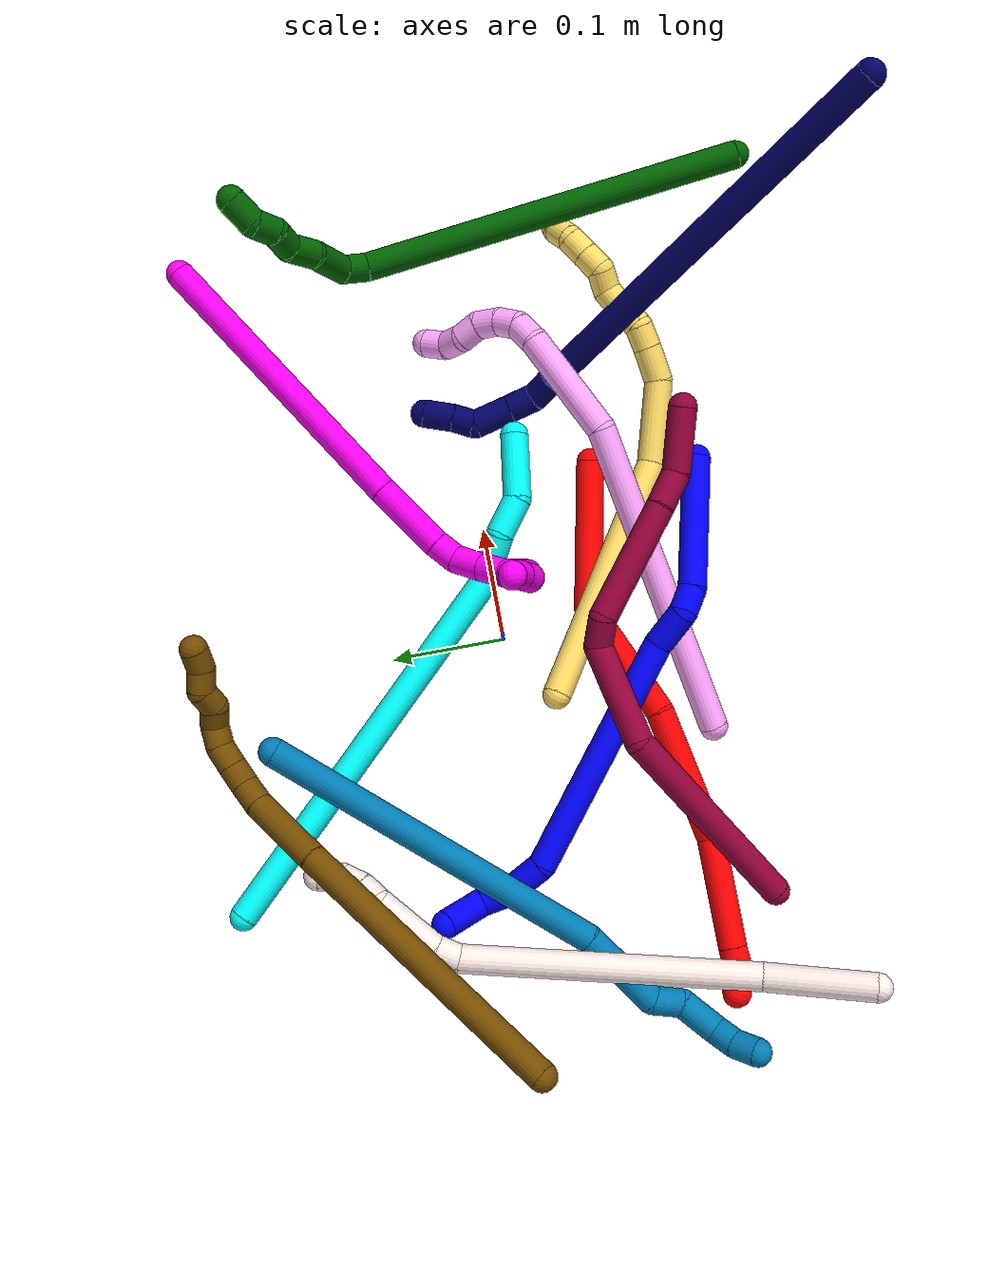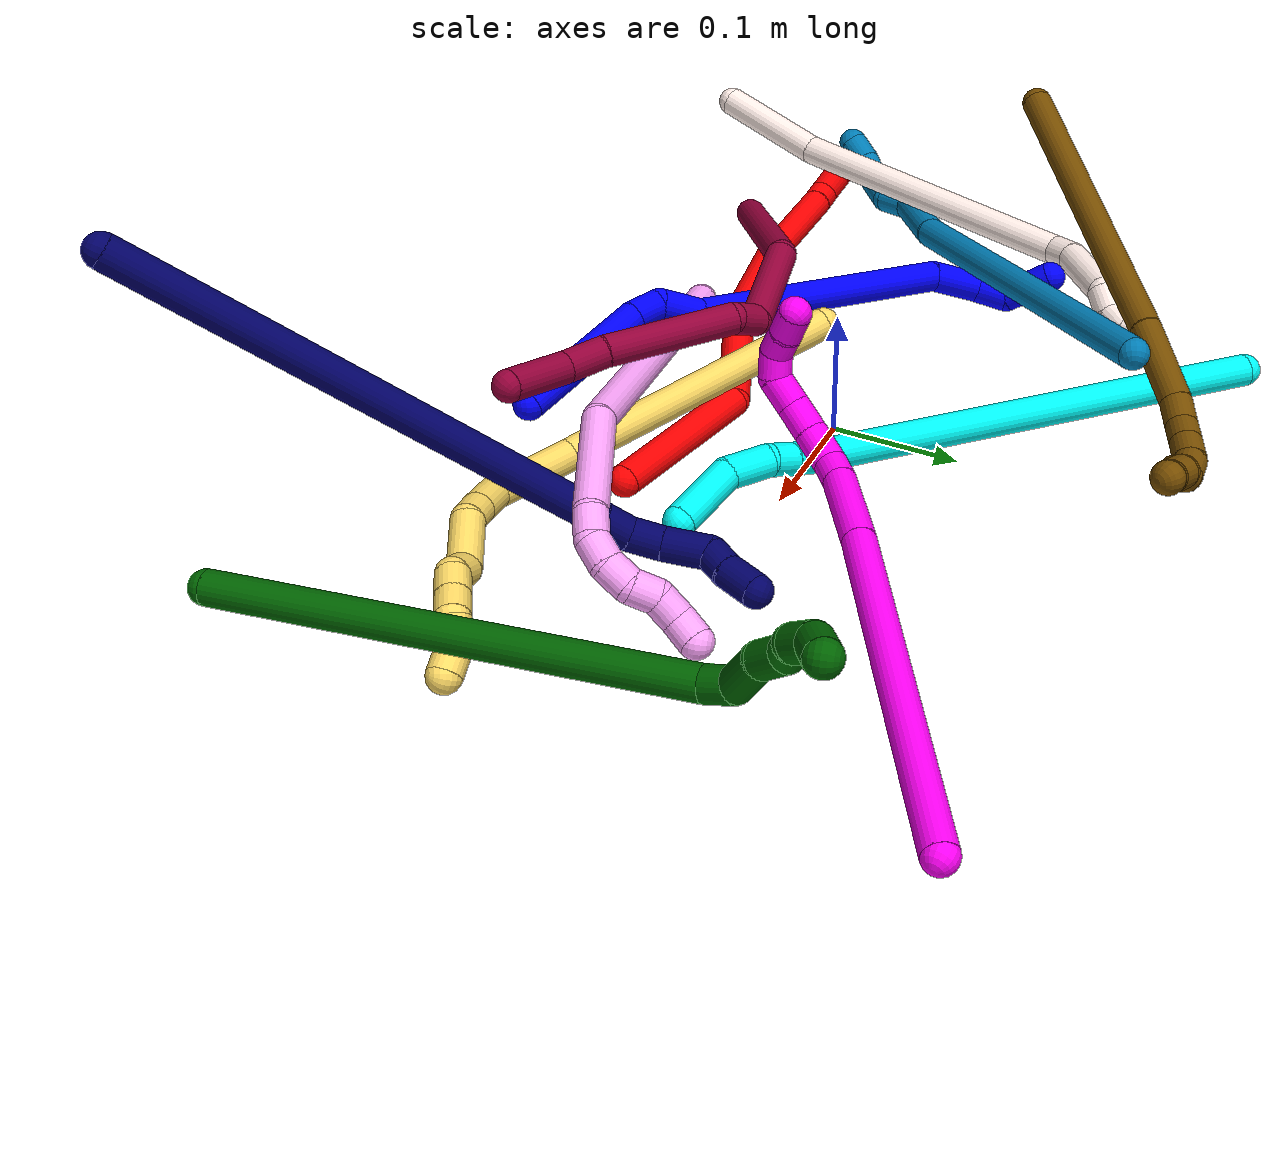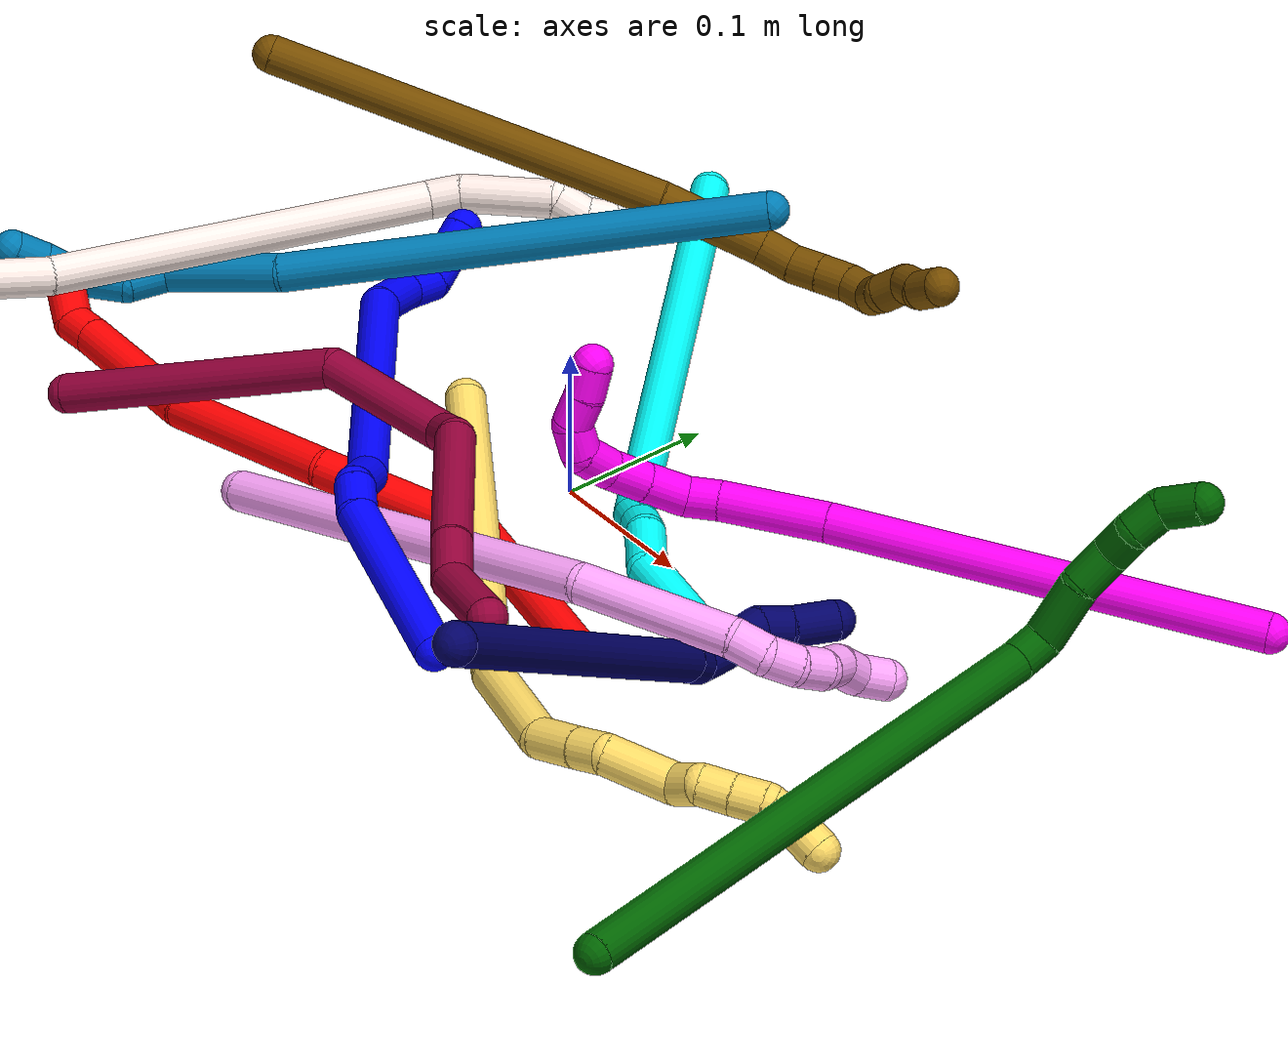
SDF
<sdf version="1.7">
 <world name="default">
  <plugin name="TubeGeneratorPlugin" filename="libtube_generator_plugin.so"/>
  <model name="photoneo_s_sensor">
   <static>1</static>
   <pose>0 0 2 1.57079 1.57079 3.14159</pose>
   <link name="link">
    <inertial><mass>0.1</mass></inertial>
    <sensor name="sensor" type="depth">
     <update_rate>30</update_rate>
     <camera>
      <horizontal_fov>1.22</horizontal_fov>
      <image><width>1920</width><height>1200</height><format>B8G8R8</format></image>
      <clip><near>0.1</near><far>4</far></clip>
      <depth_camera><output>points</output></depth_camera>
     </camera>
     <plugin name="camera_plugin" filename="libgazebo_ros_depth_camera.so">
      <baseline>0.2</baseline>
      <alwaysOn>1</alwaysOn>
      <updateRate>0.0</updateRate>
      <cameraName>camera_ir</cameraName>
      <imageTopicName>/camera/color/image_raw</imageTopicName>
      <cameraInfoTopicName>/camera/color/camera_info</cameraInfoTopicName>
      <depthImageTopicName>/camera/depth/image_raw</depthImageTopicName>
      <depthImageCameraInfoTopicName>/camera/depth/camera_info</depthImageCameraInfoTopicName>
      <pointCloudTopicName>/camera/depth/points</pointCloudTopicName>
      <frameName>fr_optical</frameName>
      <pointCloudCutoff>0.1</pointCloudCutoff>
      <pointCloudCutoffMax>2.0</pointCloudCutoffMax>
      <distortionK1>0</distortionK1>
      <distortionK2>0</distortionK2>
      <distortionK3>0</distortionK3>
      <distortionT1>0</distortionT1>
      <distortionT2>0</distortionT2>
      <CxPrime>0</CxPrime>
      <Cx>0</Cx>
      <Cy>0</Cy>
      <focalLength>0</focalLength>
      <hackBaseline>0</hackBaseline>
     </plugin>
    </sensor>
   </link>
  </model>
  <gravity>0 0 -9.8</gravity>
  <magnetic_field>6e-06 2.3e-05 -4.2e-05</magnetic_field>
  <atmosphere type="adiabatic"/>
  <physics name="default_physics" default="0" type="ode">
   <max_step_size>0.003</max_step_size>
   <real_time_factor>1</real_time_factor>
   <real_time_update_rate>1000</real_time_update_rate>
   <max_contacts>10000</max_contacts>
   <ode>
    <solver>
     <type>quick</type>
     <iters>100</iters>
     <sor>1.3</sor>
     <use_dynamic_moi_rescaling>0</use_dynamic_moi_rescaling>
    </solver>
    <constraints>
     <contact_max_correcting_vel>0</contact_max_correcting_vel>
     <contact_surface_layer>0.001</contact_surface_layer>
     <cfm>0</cfm>
     <erp>0.2</erp>
    </constraints>
   </ode>
  </physics>
  <scene><ambient>0.4 0.4 0.4 1</ambient><background>0.7 0.7 0.7 1</background><shadows>0</shadows></scene>
  <audio><device>default</device></audio>
  <spherical_coordinates>
   <surface_model>EARTH_WGS84</surface_model>
   <latitude_deg>0</latitude_deg>
   <longitude_deg>0</longitude_deg>
   <elevation>0</elevation>
   <heading_deg>0</heading_deg>
  </spherical_coordinates>
  <model name="bin">
   <static>1</static>
   <link name="bottom">
    <collision name="collision-bottom">
     <pose>0 0 -0.01 0 -0 0</pose>
     <geometry><box><size>0.8 0.6 0.02</size></box></geometry>
     <surface>
      <friction><ode><mu>100</mu><mu2>100</mu2></ode></friction>
      <contact><collide_bitmask>65535</collide_bitmask></contact>
     </surface>
    </collision>
   </link>
   <link name="west_wall">
    <collision name="collision-west_wall">
     <pose>-0.41 0 0.1 0 -0 0</pose>
     <geometry><box><size>0.02 0.6 0.2</size></box></geometry>
     <surface>
      <friction><ode><mu>100</mu><mu2>100</mu2></ode></friction>
      <contact><collide_bitmask>65535</collide_bitmask></contact>
     </surface>
    </collision>
   </link>
   <link name="east_wall">
    <collision name="collision-east_wall">
     <pose>0.41 0 0.1 0 -0 0</pose>
     <geometry><box><size>0.02 0.6 0.2</size></box></geometry>
     <surface>
      <friction><ode><mu>100</mu><mu2>100</mu2></ode></friction>
      <contact><collide_bitmask>65535</collide_bitmask></contact>
     </surface>
    </collision>
   </link>
   <link name="south_wall">
    <collision name="collision-south_wall">
     <pose>0 -0.31 0.1 0 -0 0</pose>
     <geometry><box><size>0.8 0.02 0.2</size></box></geometry>
     <surface>
      <friction><ode><mu>100</mu><mu2>100</mu2></ode></friction>
      <contact><collide_bitmask>65535</collide_bitmask></contact>
     </surface>
    </collision>
   </link>
   <link name="north_wall">
    <collision name="collision-north_wall">
     <pose>0 0.31 0.1 0 -0 0</pose>
     <geometry><box><size>0.8 0.02 0.2</size></box></geometry>
     <surface>
      <friction><ode><mu>100</mu><mu2>100</mu2></ode></friction>
      <contact><collide_bitmask>65535</collide_bitmask></contact>
     </surface>
    </collision>
   </link>
  </model>
  <model name="1">
   <static>0</static>
   <link name="1">
    <collision name="collision-cylinder-e_1_1_4">
     <pose>-0.033023 0.014927 -0.046938 -2.8337 -0.590627 2.19821</pose>
     <geometry><cylinder><radius>0.0125</radius><length>0.118601</length></cylinder></geometry>
     <surface>
      <friction><ode><mu>1.16</mu><mu2>1.16</mu2><slip1>0</slip1><slip2>0</slip2></ode></friction>
      <contact><ode><kp>1e+06</kp><kd>1</kd><max_vel>0</max_vel><min_depth>0.001</min_depth></ode></contact>
     </surface>
    </collision>
    <visual name="visual-cylinder-e_1_1_4">
     <pose>-0.033023 0.014927 -0.046938 -2.8337 -0.590627 2.19821</pose>
     <geometry><cylinder><radius>0.0125</radius><length>0.118601</length></cylinder></geometry>
     <material><ambient>0 0 1 1</ambient></material>
    </visual>
    <collision name="collision-cylinder-e_2_4_5">
     <pose>-0.069228 0.032554 -0.104809 -2.89945 -0.27531 1.70026</pose>
     <geometry><cylinder><radius>0.0125</radius><length>0.023403</length></cylinder></geometry>
     <surface>
      <friction><ode><mu>1.16</mu><mu2>1.16</mu2><slip1>0</slip1><slip2>0</slip2></ode></friction>
      <contact><ode><kp>1e+06</kp><kd>1</kd><max_vel>0</max_vel><min_depth>0.001</min_depth></ode></contact>
     </surface>
    </collision>
    <visual name="visual-cylinder-e_2_4_5">
     <pose>-0.069228 0.032554 -0.104809 -2.89945 -0.27531 1.70026</pose>
     <geometry><cylinder><radius>0.0125</radius><length>0.023403</length></cylinder></geometry>
     <material><ambient>0 0 1 1</ambient></material>
    </visual>
    <collision name="collision-cylinder-e_3_5_6">
     <pose>-0.072811 0.028892 -0.132498 2.77877 -0.022425 -0.122109</pose>
     <geometry><cylinder><radius>0.0125</radius><length>0.035855</length></cylinder></geometry>
     <surface>
      <friction><ode><mu>1.16</mu><mu2>1.16</mu2><slip1>0</slip1><slip2>0</slip2></ode></friction>
      <contact><ode><kp>1e+06</kp><kd>1</kd><max_vel>0</max_vel><min_depth>0.001</min_depth></ode></contact>
     </surface>
    </collision>
    <visual name="visual-cylinder-e_3_5_6">
     <pose>-0.072811 0.028892 -0.132498 2.77877 -0.022425 -0.122109</pose>
     <geometry><cylinder><radius>0.0125</radius><length>0.035855</length></cylinder></geometry>
     <material><ambient>0 0 1 1</ambient></material>
    </visual>
    <collision name="collision-cylinder-e_4_6_7">
     <pose>-0.093492 0.019986 -0.255371 3.11761 -0.188774 -2.88958</pose>
     <geometry><cylinder><radius>0.0125</radius><length>0.216136</length></cylinder></geometry>
     <surface>
      <friction><ode><mu>1.16</mu><mu2>1.16</mu2><slip1>0</slip1><slip2>0</slip2></ode></friction>
      <contact><ode><kp>1e+06</kp><kd>1</kd><max_vel>0</max_vel><min_depth>0.001</min_depth></ode></contact>
     </surface>
    </collision>
    <visual name="visual-cylinder-e_4_6_7">
     <pose>-0.093492 0.019986 -0.255371 3.11761 -0.188774 -2.88958</pose>
     <geometry><cylinder><radius>0.0125</radius><length>0.216136</length></cylinder></geometry>
     <material><ambient>0 0 1 1</ambient></material>
    </visual>
    <collision name="collision-cylinder-e_5_7_8">
     <pose>-0.110036 0.012497 -0.380348 2.88527 0.189346 1.27005</pose>
     <geometry><cylinder><radius>0.0125</radius><length>0.039701</length></cylinder></geometry>
     <surface>
      <friction><ode><mu>1.16</mu><mu2>1.16</mu2><slip1>0</slip1><slip2>0</slip2></ode></friction>
      <contact><ode><kp>1e+06</kp><kd>1</kd><max_vel>0</max_vel><min_depth>0.001</min_depth></ode></contact>
     </surface>
    </collision>
    <visual name="visual-cylinder-e_5_7_8">
     <pose>-0.110036 0.012497 -0.380348 2.88527 0.189346 1.27005</pose>
     <geometry><cylinder><radius>0.0125</radius><length>0.039701</length></cylinder></geometry>
     <material><ambient>0 0 1 1</ambient></material>
    </visual>
    <collision name="collision-cylinder-e_6_8_9">
     <pose>-0.100092 0.005452 -0.410248 2.95337 0.504592 2.4396</pose>
     <geometry><cylinder><radius>0.0125</radius><length>0.02568</length></cylinder></geometry>
     <surface>
      <friction><ode><mu>1.16</mu><mu2>1.16</mu2><slip1>0</slip1><slip2>0</slip2></ode></friction>
      <contact><ode><kp>1e+06</kp><kd>1</kd><max_vel>0</max_vel><min_depth>0.001</min_depth></ode></contact>
     </surface>
    </collision>
    <visual name="visual-cylinder-e_6_8_9">
     <pose>-0.100092 0.005452 -0.410248 2.95337 0.504592 2.4396</pose>
     <geometry><cylinder><radius>0.0125</radius><length>0.02568</length></cylinder></geometry>
     <material><ambient>0 0 1 1</ambient></material>
    </visual>
    <collision name="collision-cylinder-e_7_9_2">
     <pose>-0.086749 0.014937 -0.436368 -2.48634 0.358929 -0.980596</pose>
     <geometry><cylinder><radius>0.0125</radius><length>0.040624</length></cylinder></geometry>
     <surface>
      <friction><ode><mu>1.16</mu><mu2>1.16</mu2><slip1>0</slip1><slip2>0</slip2></ode></friction>
      <contact><ode><kp>1e+06</kp><kd>1</kd><max_vel>0</max_vel><min_depth>0.001</min_depth></ode></contact>
     </surface>
    </collision>
    <visual name="visual-cylinder-e_7_9_2">
     <pose>-0.086749 0.014937 -0.436368 -2.48634 0.358929 -0.980596</pose>
     <geometry><cylinder><radius>0.0125</radius><length>0.040624</length></cylinder></geometry>
     <material><ambient>0 0 1 1</ambient></material>
    </visual>
    <collision name="collision-sphere-2">
     <pose>-0.079614 0.026525 -0.451447 0 -0 0</pose>
     <geometry><sphere><radius>0.0125</radius></sphere></geometry>
     <surface>
      <friction><ode><mu>1.16</mu><mu2>1.16</mu2><slip1>0</slip1><slip2>0</slip2></ode></friction>
      <contact><ode><kp>1e+06</kp><kd>1</kd><max_vel>0</max_vel><min_depth>0.001</min_depth></ode></contact>
     </surface>
    </collision>
    <visual name="visual-sphere-2">
     <pose>-0.079614 0.026525 -0.451447 0 -0 0</pose>
     <geometry><sphere><radius>0.0125</radius></sphere></geometry>
     <material><ambient>0 0 1 1</ambient></material>
    </visual>
    <collision name="collision-sphere-9">
     <pose>-0.093884 0.003348 -0.421289 0 -0 0</pose>
     <geometry><sphere><radius>0.0125</radius></sphere></geometry>
     <surface>
      <friction><ode><mu>1.16</mu><mu2>1.16</mu2><slip1>0</slip1><slip2>0</slip2></ode></friction>
      <contact><ode><kp>1e+06</kp><kd>1</kd><max_vel>0</max_vel><min_depth>0.001</min_depth></ode></contact>
     </surface>
    </collision>
    <visual name="visual-sphere-9">
     <pose>-0.093884 0.003348 -0.421289 0 -0 0</pose>
     <geometry><sphere><radius>0.0125</radius></sphere></geometry>
     <material><ambient>0 0 1 1</ambient></material>
    </visual>
    <collision name="collision-sphere-4">
     <pose>-0.066047 0.029853 -0.093877 0 -0 0</pose>
     <geometry><sphere><radius>0.0125</radius></sphere></geometry>
     <surface>
      <friction><ode><mu>1.16</mu><mu2>1.16</mu2><slip1>0</slip1><slip2>0</slip2></ode></friction>
      <contact><ode><kp>1e+06</kp><kd>1</kd><max_vel>0</max_vel><min_depth>0.001</min_depth></ode></contact>
     </surface>
    </collision>
    <visual name="visual-sphere-4">
     <pose>-0.066047 0.029853 -0.093877 0 -0 0</pose>
     <geometry><sphere><radius>0.0125</radius></sphere></geometry>
     <material><ambient>0 0 1 1</ambient></material>
    </visual>
    <collision name="collision-sphere-1">
     <geometry><sphere><radius>0.0125</radius></sphere></geometry>
     <surface>
      <friction><ode><mu>1.16</mu><mu2>1.16</mu2><slip1>0</slip1><slip2>0</slip2></ode></friction>
      <contact><ode><kp>1e+06</kp><kd>1</kd><max_vel>0</max_vel><min_depth>0.001</min_depth></ode></contact>
     </surface>
    </collision>
    <visual name="visual-sphere-1">
     <geometry><sphere><radius>0.0125</radius></sphere></geometry>
     <material><ambient>0 0 1 1</ambient></material>
    </visual>
    <collision name="collision-sphere-8">
     <pose>-0.106299 0.007555 -0.399206 0 -0 0</pose>
     <geometry><sphere><radius>0.0125</radius></sphere></geometry>
     <surface>
      <friction><ode><mu>1.16</mu><mu2>1.16</mu2><slip1>0</slip1><slip2>0</slip2></ode></friction>
      <contact><ode><kp>1e+06</kp><kd>1</kd><max_vel>0</max_vel><min_depth>0.001</min_depth></ode></contact>
     </surface>
    </collision>
    <visual name="visual-sphere-8">
     <pose>-0.106299 0.007555 -0.399206 0 -0 0</pose>
     <geometry><sphere><radius>0.0125</radius></sphere></geometry>
     <material><ambient>0 0 1 1</ambient></material>
    </visual>
    <collision name="collision-sphere-5">
     <pose>-0.072409 0.035254 -0.115741 0 -0 0</pose>
     <geometry><sphere><radius>0.0125</radius></sphere></geometry>
     <surface>
      <friction><ode><mu>1.16</mu><mu2>1.16</mu2><slip1>0</slip1><slip2>0</slip2></ode></friction>
      <contact><ode><kp>1e+06</kp><kd>1</kd><max_vel>0</max_vel><min_depth>0.001</min_depth></ode></contact>
     </surface>
    </collision>
    <visual name="visual-sphere-5">
     <pose>-0.072409 0.035254 -0.115741 0 -0 0</pose>
     <geometry><sphere><radius>0.0125</radius></sphere></geometry>
     <material><ambient>0 0 1 1</ambient></material>
    </visual>
    <collision name="collision-sphere-6">
     <pose>-0.073213 0.022531 -0.149254 0 -0 0</pose>
     <geometry><sphere><radius>0.0125</radius></sphere></geometry>
     <surface>
      <friction><ode><mu>1.16</mu><mu2>1.16</mu2><slip1>0</slip1><slip2>0</slip2></ode></friction>
      <contact><ode><kp>1e+06</kp><kd>1</kd><max_vel>0</max_vel><min_depth>0.001</min_depth></ode></contact>
     </surface>
    </collision>
    <visual name="visual-sphere-6">
     <pose>-0.073213 0.022531 -0.149254 0 -0 0</pose>
     <geometry><sphere><radius>0.0125</radius></sphere></geometry>
     <material><ambient>0 0 1 1</ambient></material>
    </visual>
    <collision name="collision-sphere-7">
     <pose>-0.113772 0.01744 -0.361489 0 -0 0</pose>
     <geometry><sphere><radius>0.0125</radius></sphere></geometry>
     <surface>
      <friction><ode><mu>1.16</mu><mu2>1.16</mu2><slip1>0</slip1><slip2>0</slip2></ode></friction>
      <contact><ode><kp>1e+06</kp><kd>1</kd><max_vel>0</max_vel><min_depth>0.001</min_depth></ode></contact>
     </surface>
    </collision>
    <visual name="visual-sphere-7">
     <pose>-0.113772 0.01744 -0.361489 0 -0 0</pose>
     <geometry><sphere><radius>0.0125</radius></sphere></geometry>
     <material><ambient>0 0 1 1</ambient></material>
    </visual>
    <inertial>
     <pose>-0.077635 0.018261 -0.222655 0 -0 0</pose>
     <mass>0.5</mass>
     <inertia>
      <ixx>-0.000984</ixx>
      <ixy>0</ixy>
      <ixz>0</ixz>
      <iyy>0.000812</iyy>
      <iyz>0</iyz>
      <izz>0.000183</izz>
     </inertia>
    </inertial>
   </link>
   <pose>0.122886 -0.194764 0.041941 1.49937 -0.03997 0.716982</pose>
  </model>
  <model name="2">
   <static>0</static>
   <link name="2">
    <collision name="collision-cylinder-e_1_1_4">
     <pose>0.029121 -0.027437 0.051621 0.488535 0.462158 0.117151</pose>
     <geometry><cylinder><radius>0.0125</radius><length>0.130621</length></cylinder></geometry>
     <surface>
      <friction><ode><mu>1.16</mu><mu2>1.16</mu2><slip1>0</slip1><slip2>0</slip2></ode></friction>
      <contact><ode><kp>1e+06</kp><kd>1</kd><max_vel>0</max_vel><min_depth>0.001</min_depth></ode></contact>
     </surface>
    </collision>
    <visual name="visual-cylinder-e_1_1_4">
     <pose>0.029121 -0.027437 0.051621 0.488535 0.462158 0.117151</pose>
     <geometry><cylinder><radius>0.0125</radius><length>0.130621</length></cylinder></geometry>
     <material><ambient>1 0 0 1</ambient></material>
    </visual>
    <collision name="collision-cylinder-e_2_4_5">
     <pose>0.075035 -0.103046 0.125677 1.13494 0.306087 0.19601</pose>
     <geometry><cylinder><radius>0.0125</radius><length>0.111463</length></cylinder></geometry>
     <surface>
      <friction><ode><mu>1.16</mu><mu2>1.16</mu2><slip1>0</slip1><slip2>0</slip2></ode></friction>
      <contact><ode><kp>1e+06</kp><kd>1</kd><max_vel>0</max_vel><min_depth>0.001</min_depth></ode></contact>
     </surface>
    </collision>
    <visual name="visual-cylinder-e_2_4_5">
     <pose>0.075035 -0.103046 0.125677 1.13494 0.306087 0.19601</pose>
     <geometry><cylinder><radius>0.0125</radius><length>0.111463</length></cylinder></geometry>
     <material><ambient>1 0 0 1</ambient></material>
    </visual>
    <collision name="collision-cylinder-e_3_5_6">
     <pose>0.106567 -0.195218 0.185491 0.866563 0.249953 0.116103</pose>
     <geometry><cylinder><radius>0.0125</radius><length>0.119168</length></cylinder></geometry>
     <surface>
      <friction><ode><mu>1.16</mu><mu2>1.16</mu2><slip1>0</slip1><slip2>0</slip2></ode></friction>
      <contact><ode><kp>1e+06</kp><kd>1</kd><max_vel>0</max_vel><min_depth>0.001</min_depth></ode></contact>
     </surface>
    </collision>
    <visual name="visual-cylinder-e_3_5_6">
     <pose>0.106567 -0.195218 0.185491 0.866563 0.249953 0.116103</pose>
     <geometry><cylinder><radius>0.0125</radius><length>0.119168</length></cylinder></geometry>
     <material><ambient>1 0 0 1</ambient></material>
    </visual>
    <collision name="collision-cylinder-e_4_6_7">
     <pose>0.141103 -0.267924 0.25611 0.712359 0.423466 0.159607</pose>
     <geometry><cylinder><radius>0.0125</radius><length>0.096352</length></cylinder></geometry>
     <surface>
      <friction><ode><mu>1.16</mu><mu2>1.16</mu2><slip1>0</slip1><slip2>0</slip2></ode></friction>
      <contact><ode><kp>1e+06</kp><kd>1</kd><max_vel>0</max_vel><min_depth>0.001</min_depth></ode></contact>
     </surface>
    </collision>
    <visual name="visual-cylinder-e_4_6_7">
     <pose>0.141103 -0.267924 0.25611 0.712359 0.423466 0.159607</pose>
     <geometry><cylinder><radius>0.0125</radius><length>0.096352</length></cylinder></geometry>
     <material><ambient>1 0 0 1</ambient></material>
    </visual>
    <collision name="collision-cylinder-e_5_7_8">
     <pose>0.164973 -0.303261 0.296174 0.770921 0.404573 0.166053</pose>
     <geometry><cylinder><radius>0.0125</radius><length>0.0207</length></cylinder></geometry>
     <surface>
      <friction><ode><mu>1.16</mu><mu2>1.16</mu2><slip1>0</slip1><slip2>0</slip2></ode></friction>
      <contact><ode><kp>1e+06</kp><kd>1</kd><max_vel>0</max_vel><min_depth>0.001</min_depth></ode></contact>
     </surface>
    </collision>
    <visual name="visual-cylinder-e_5_7_8">
     <pose>0.164973 -0.303261 0.296174 0.770921 0.404573 0.166053</pose>
     <geometry><cylinder><radius>0.0125</radius><length>0.0207</length></cylinder></geometry>
     <material><ambient>1 0 0 1</ambient></material>
    </visual>
    <collision name="collision-cylinder-e_6_8_2">
     <pose>0.178754 -0.312373 0.307156 0.538374 1.10808 0.338108</pose>
     <geometry><cylinder><radius>0.0125</radius><length>0.021695</length></cylinder></geometry>
     <surface>
      <friction><ode><mu>1.16</mu><mu2>1.16</mu2><slip1>0</slip1><slip2>0</slip2></ode></friction>
      <contact><ode><kp>1e+06</kp><kd>1</kd><max_vel>0</max_vel><min_depth>0.001</min_depth></ode></contact>
     </surface>
    </collision>
    <visual name="visual-cylinder-e_6_8_2">
     <pose>0.178754 -0.312373 0.307156 0.538374 1.10808 0.338108</pose>
     <geometry><cylinder><radius>0.0125</radius><length>0.021695</length></cylinder></geometry>
     <material><ambient>1 0 0 1</ambient></material>
    </visual>
    <collision name="collision-sphere-2">
     <pose>0.188461 -0.314856 0.311313 0 -0 0</pose>
     <geometry><sphere><radius>0.0125</radius></sphere></geometry>
     <surface>
      <friction><ode><mu>1.16</mu><mu2>1.16</mu2><slip1>0</slip1><slip2>0</slip2></ode></friction>
      <contact><ode><kp>1e+06</kp><kd>1</kd><max_vel>0</max_vel><min_depth>0.001</min_depth></ode></contact>
     </surface>
    </collision>
    <visual name="visual-sphere-2">
     <pose>0.188461 -0.314856 0.311313 0 -0 0</pose>
     <geometry><sphere><radius>0.0125</radius></sphere></geometry>
     <material><ambient>1 0 0 1</ambient></material>
    </visual>
    <collision name="collision-sphere-4">
     <pose>0.058242 -0.054874 0.103241 0 -0 0</pose>
     <geometry><sphere><radius>0.0125</radius></sphere></geometry>
     <surface>
      <friction><ode><mu>1.16</mu><mu2>1.16</mu2><slip1>0</slip1><slip2>0</slip2></ode></friction>
      <contact><ode><kp>1e+06</kp><kd>1</kd><max_vel>0</max_vel><min_depth>0.001</min_depth></ode></contact>
     </surface>
    </collision>
    <visual name="visual-sphere-4">
     <pose>0.058242 -0.054874 0.103241 0 -0 0</pose>
     <geometry><sphere><radius>0.0125</radius></sphere></geometry>
     <material><ambient>1 0 0 1</ambient></material>
    </visual>
    <collision name="collision-sphere-1">
     <geometry><sphere><radius>0.0125</radius></sphere></geometry>
     <surface>
      <friction><ode><mu>1.16</mu><mu2>1.16</mu2><slip1>0</slip1><slip2>0</slip2></ode></friction>
      <contact><ode><kp>1e+06</kp><kd>1</kd><max_vel>0</max_vel><min_depth>0.001</min_depth></ode></contact>
     </surface>
    </collision>
    <visual name="visual-sphere-1">
     <geometry><sphere><radius>0.0125</radius></sphere></geometry>
     <material><ambient>1 0 0 1</ambient></material>
    </visual>
    <collision name="collision-sphere-8">
     <pose>0.169047 -0.30989 0.302999 0 -0 0</pose>
     <geometry><sphere><radius>0.0125</radius></sphere></geometry>
     <surface>
      <friction><ode><mu>1.16</mu><mu2>1.16</mu2><slip1>0</slip1><slip2>0</slip2></ode></friction>
      <contact><ode><kp>1e+06</kp><kd>1</kd><max_vel>0</max_vel><min_depth>0.001</min_depth></ode></contact>
     </surface>
    </collision>
    <visual name="visual-sphere-8">
     <pose>0.169047 -0.30989 0.302999 0 -0 0</pose>
     <geometry><sphere><radius>0.0125</radius></sphere></geometry>
     <material><ambient>1 0 0 1</ambient></material>
    </visual>
    <collision name="collision-sphere-5">
     <pose>0.091829 -0.151219 0.148112 0 -0 0</pose>
     <geometry><sphere><radius>0.0125</radius></sphere></geometry>
     <surface>
      <friction><ode><mu>1.16</mu><mu2>1.16</mu2><slip1>0</slip1><slip2>0</slip2></ode></friction>
      <contact><ode><kp>1e+06</kp><kd>1</kd><max_vel>0</max_vel><min_depth>0.001</min_depth></ode></contact>
     </surface>
    </collision>
    <visual name="visual-sphere-5">
     <pose>0.091829 -0.151219 0.148112 0 -0 0</pose>
     <geometry><sphere><radius>0.0125</radius></sphere></geometry>
     <material><ambient>1 0 0 1</ambient></material>
    </visual>
    <collision name="collision-sphere-6">
     <pose>0.121306 -0.239216 0.22287 0 -0 0</pose>
     <geometry><sphere><radius>0.0125</radius></sphere></geometry>
     <surface>
      <friction><ode><mu>1.16</mu><mu2>1.16</mu2><slip1>0</slip1><slip2>0</slip2></ode></friction>
      <contact><ode><kp>1e+06</kp><kd>1</kd><max_vel>0</max_vel><min_depth>0.001</min_depth></ode></contact>
     </surface>
    </collision>
    <visual name="visual-sphere-6">
     <pose>0.121306 -0.239216 0.22287 0 -0 0</pose>
     <geometry><sphere><radius>0.0125</radius></sphere></geometry>
     <material><ambient>1 0 0 1</ambient></material>
    </visual>
    <collision name="collision-sphere-7">
     <pose>0.160899 -0.296631 0.28935 0 -0 0</pose>
     <geometry><sphere><radius>0.0125</radius></sphere></geometry>
     <surface>
      <friction><ode><mu>1.16</mu><mu2>1.16</mu2><slip1>0</slip1><slip2>0</slip2></ode></friction>
      <contact><ode><kp>1e+06</kp><kd>1</kd><max_vel>0</max_vel><min_depth>0.001</min_depth></ode></contact>
     </surface>
    </collision>
    <visual name="visual-sphere-7">
     <pose>0.160899 -0.296631 0.28935 0 -0 0</pose>
     <geometry><sphere><radius>0.0125</radius></sphere></geometry>
     <material><ambient>1 0 0 1</ambient></material>
    </visual>
    <inertial>
     <pose>0.091511 -0.154406 0.160654 0 -0 0</pose>
     <mass>0.5</mass>
     <inertia>
      <ixx>0.00058</ixx>
      <ixy>0</ixy>
      <ixz>0</ixz>
      <iyy>0.000435</iyy>
      <iyz>0</iyz>
      <izz>0.000172</izz>
     </inertia>
    </inertial>
   </link>
   <pose>0.141645 -0.105219 0.012613 -3.06785 -1.03101 2.44037</pose>
  </model>
  <model name="3">
   <static>0</static>
   <link name="3">
    <collision name="collision-cylinder-e_1_1_4">
     <pose>0.104138 -0.108624 -0.102714 2.32824 0.608435 1.25983</pose>
     <geometry><cylinder><radius>0.0125</radius><length>0.364385</length></cylinder></geometry>
     <surface>
      <friction><ode><mu>1.16</mu><mu2>1.16</mu2><slip1>0</slip1><slip2>0</slip2></ode></friction>
      <contact><ode><kp>1e+06</kp><kd>1</kd><max_vel>0</max_vel><min_depth>0.001</min_depth></ode></contact>
     </surface>
    </collision>
    <visual name="visual-cylinder-e_1_1_4">
     <pose>0.104138 -0.108624 -0.102714 2.32824 0.608435 1.25983</pose>
     <geometry><cylinder><radius>0.0125</radius><length>0.364385</length></cylinder></geometry>
     <material><ambient>0.003922 1 0.996078 1</ambient></material>
    </visual>
    <collision name="collision-cylinder-e_2_4_5">
     <pose>0.209643 -0.224105 -0.213383 2.43009 0.129393 0.345256</pose>
     <geometry><cylinder><radius>0.0125</radius><length>0.021183</length></cylinder></geometry>
     <surface>
      <friction><ode><mu>1.16</mu><mu2>1.16</mu2><slip1>0</slip1><slip2>0</slip2></ode></friction>
      <contact><ode><kp>1e+06</kp><kd>1</kd><max_vel>0</max_vel><min_depth>0.001</min_depth></ode></contact>
     </surface>
    </collision>
    <visual name="visual-cylinder-e_2_4_5">
     <pose>0.209643 -0.224105 -0.213383 2.43009 0.129393 0.345256</pose>
     <geometry><cylinder><radius>0.0125</radius><length>0.021183</length></cylinder></geometry>
     <material><ambient>0.003922 1 0.996078 1</ambient></material>
    </visual>
    <collision name="collision-cylinder-e_3_5_6">
     <pose>0.212839 -0.237364 -0.229285 2.46359 0.17737 0.494039</pose>
     <geometry><cylinder><radius>0.0125</radius><length>0.020735</length></cylinder></geometry>
     <surface>
      <friction><ode><mu>1.16</mu><mu2>1.16</mu2><slip1>0</slip1><slip2>0</slip2></ode></friction>
      <contact><ode><kp>1e+06</kp><kd>1</kd><max_vel>0</max_vel><min_depth>0.001</min_depth></ode></contact>
     </surface>
    </collision>
    <visual name="visual-cylinder-e_3_5_6">
     <pose>0.212839 -0.237364 -0.229285 2.46359 0.17737 0.494039</pose>
     <geometry><cylinder><radius>0.0125</radius><length>0.020735</length></cylinder></geometry>
     <material><ambient>0.003922 1 0.996078 1</ambient></material>
    </visual>
    <collision name="collision-cylinder-e_4_6_7">
     <pose>0.222633 -0.256225 -0.246723 2.22172 0.470468 0.901249</pose>
     <geometry><cylinder><radius>0.0125</radius><length>0.035142</length></cylinder></geometry>
     <surface>
      <friction><ode><mu>1.16</mu><mu2>1.16</mu2><slip1>0</slip1><slip2>0</slip2></ode></friction>
      <contact><ode><kp>1e+06</kp><kd>1</kd><max_vel>0</max_vel><min_depth>0.001</min_depth></ode></contact>
     </surface>
    </collision>
    <visual name="visual-cylinder-e_4_6_7">
     <pose>0.222633 -0.256225 -0.246723 2.22172 0.470468 0.901249</pose>
     <geometry><cylinder><radius>0.0125</radius><length>0.035142</length></cylinder></geometry>
     <material><ambient>0.003922 1 0.996078 1</ambient></material>
    </visual>
    <collision name="collision-cylinder-e_5_7_2">
     <pose>0.232909 -0.296415 -0.265316 1.88796 0.078997 0.109023</pose>
     <geometry><cylinder><radius>0.0125</radius><length>0.058555</length></cylinder></geometry>
     <surface>
      <friction><ode><mu>1.16</mu><mu2>1.16</mu2><slip1>0</slip1><slip2>0</slip2></ode></friction>
      <contact><ode><kp>1e+06</kp><kd>1</kd><max_vel>0</max_vel><min_depth>0.001</min_depth></ode></contact>
     </surface>
    </collision>
    <visual name="visual-cylinder-e_5_7_2">
     <pose>0.232909 -0.296415 -0.265316 1.88796 0.078997 0.109023</pose>
     <geometry><cylinder><radius>0.0125</radius><length>0.058555</length></cylinder></geometry>
     <material><ambient>0.003922 1 0.996078 1</ambient></material>
    </visual>
    <collision name="collision-sphere-2">
     <pose>0.235219 -0.324146 -0.274418 0 -0 0</pose>
     <geometry><sphere><radius>0.0125</radius></sphere></geometry>
     <surface>
      <friction><ode><mu>1.16</mu><mu2>1.16</mu2><slip1>0</slip1><slip2>0</slip2></ode></friction>
      <contact><ode><kp>1e+06</kp><kd>1</kd><max_vel>0</max_vel><min_depth>0.001</min_depth></ode></contact>
     </surface>
    </collision>
    <visual name="visual-sphere-2">
     <pose>0.235219 -0.324146 -0.274418 0 -0 0</pose>
     <geometry><sphere><radius>0.0125</radius></sphere></geometry>
     <material><ambient>0.003922 1 0.996078 1</ambient></material>
    </visual>
    <collision name="collision-sphere-7">
     <pose>0.230598 -0.268684 -0.256213 0 -0 0</pose>
     <geometry><sphere><radius>0.0125</radius></sphere></geometry>
     <surface>
      <friction><ode><mu>1.16</mu><mu2>1.16</mu2><slip1>0</slip1><slip2>0</slip2></ode></friction>
      <contact><ode><kp>1e+06</kp><kd>1</kd><max_vel>0</max_vel><min_depth>0.001</min_depth></ode></contact>
     </surface>
    </collision>
    <visual name="visual-sphere-7">
     <pose>0.230598 -0.268684 -0.256213 0 -0 0</pose>
     <geometry><sphere><radius>0.0125</radius></sphere></geometry>
     <material><ambient>0.003922 1 0.996078 1</ambient></material>
    </visual>
    <collision name="collision-sphere-6">
     <pose>0.214668 -0.243765 -0.237233 0 -0 0</pose>
     <geometry><sphere><radius>0.0125</radius></sphere></geometry>
     <surface>
      <friction><ode><mu>1.16</mu><mu2>1.16</mu2><slip1>0</slip1><slip2>0</slip2></ode></friction>
      <contact><ode><kp>1e+06</kp><kd>1</kd><max_vel>0</max_vel><min_depth>0.001</min_depth></ode></contact>
     </surface>
    </collision>
    <visual name="visual-sphere-6">
     <pose>0.214668 -0.243765 -0.237233 0 -0 0</pose>
     <geometry><sphere><radius>0.0125</radius></sphere></geometry>
     <material><ambient>0.003922 1 0.996078 1</ambient></material>
    </visual>
    <collision name="collision-sphere-5">
     <pose>0.21101 -0.230963 -0.221337 0 -0 0</pose>
     <geometry><sphere><radius>0.0125</radius></sphere></geometry>
     <surface>
      <friction><ode><mu>1.16</mu><mu2>1.16</mu2><slip1>0</slip1><slip2>0</slip2></ode></friction>
      <contact><ode><kp>1e+06</kp><kd>1</kd><max_vel>0</max_vel><min_depth>0.001</min_depth></ode></contact>
     </surface>
    </collision>
    <visual name="visual-sphere-5">
     <pose>0.21101 -0.230963 -0.221337 0 -0 0</pose>
     <geometry><sphere><radius>0.0125</radius></sphere></geometry>
     <material><ambient>0.003922 1 0.996078 1</ambient></material>
    </visual>
    <collision name="collision-sphere-1">
     <geometry><sphere><radius>0.0125</radius></sphere></geometry>
     <surface>
      <friction><ode><mu>1.16</mu><mu2>1.16</mu2><slip1>0</slip1><slip2>0</slip2></ode></friction>
      <contact><ode><kp>1e+06</kp><kd>1</kd><max_vel>0</max_vel><min_depth>0.001</min_depth></ode></contact>
     </surface>
    </collision>
    <visual name="visual-sphere-1">
     <geometry><sphere><radius>0.0125</radius></sphere></geometry>
     <material><ambient>0.003922 1 0.996078 1</ambient></material>
    </visual>
    <collision name="collision-sphere-4">
     <pose>0.208276 -0.217247 -0.205428 0 -0 0</pose>
     <geometry><sphere><radius>0.0125</radius></sphere></geometry>
     <surface>
      <friction><ode><mu>1.16</mu><mu2>1.16</mu2><slip1>0</slip1><slip2>0</slip2></ode></friction>
      <contact><ode><kp>1e+06</kp><kd>1</kd><max_vel>0</max_vel><min_depth>0.001</min_depth></ode></contact>
     </surface>
    </collision>
    <visual name="visual-sphere-4">
     <pose>0.208276 -0.217247 -0.205428 0 -0 0</pose>
     <geometry><sphere><radius>0.0125</radius></sphere></geometry>
     <material><ambient>0.003922 1 0.996078 1</ambient></material>
    </visual>
    <inertial>
     <pose>0.136525 -0.151221 -0.141816 0 -0 0</pose>
     <mass>0.5</mass>
     <inertia>
      <ixx>0.004226</ixx>
      <ixy>0</ixy>
      <ixz>0</ixz>
      <iyy>0.003883</iyy>
      <iyz>0</iyz>
      <izz>9.7e-05</izz>
     </inertia>
    </inertial>
   </link>
   <pose>-0.197233 0.26745 0.011979 2.76976 0.497132 -1.66702</pose>
  </model>
  <model name="4">
   <static>0</static>
   <link name="4">
    <collision name="collision-cylinder-e_1_1_4">
     <pose>0.036875 -0.132948 0.023148 1.39841 0.266742 0.224701</pose>
     <geometry><cylinder><radius>0.0125</radius><length>0.279791</length></cylinder></geometry>
     <surface>
      <friction><ode><mu>1.16</mu><mu2>1.16</mu2><slip1>0</slip1><slip2>0</slip2></ode></friction>
      <contact><ode><kp>1e+06</kp><kd>1</kd><max_vel>0</max_vel><min_depth>0.001</min_depth></ode></contact>
     </surface>
    </collision>
    <visual name="visual-cylinder-e_1_1_4">
     <pose>0.036875 -0.132948 0.023148 1.39841 0.266742 0.224701</pose>
     <geometry><cylinder><radius>0.0125</radius><length>0.279791</length></cylinder></geometry>
     <material><ambient>1 0.65098 0.996078 1</ambient></material>
    </visual>
    <collision name="collision-cylinder-e_2_4_5">
     <pose>0.074588 -0.314566 0.040399 1.69137 0.017082 0.019277</pose>
     <geometry><cylinder><radius>0.0125</radius><length>0.098068</length></cylinder></geometry>
     <surface>
      <friction><ode><mu>1.16</mu><mu2>1.16</mu2><slip1>0</slip1><slip2>0</slip2></ode></friction>
      <contact><ode><kp>1e+06</kp><kd>1</kd><max_vel>0</max_vel><min_depth>0.001</min_depth></ode></contact>
     </surface>
    </collision>
    <visual name="visual-cylinder-e_2_4_5">
     <pose>0.074588 -0.314566 0.040399 1.69137 0.017082 0.019277</pose>
     <geometry><cylinder><radius>0.0125</radius><length>0.098068</length></cylinder></geometry>
     <material><ambient>1 0.65098 0.996078 1</ambient></material>
    </visual>
    <collision name="collision-cylinder-e_3_5_6">
     <pose>0.072866 -0.373397 0.031907 1.82088 -0.239402 -0.307279</pose>
     <geometry><cylinder><radius>0.0125</radius><length>0.021588</length></cylinder></geometry>
     <surface>
      <friction><ode><mu>1.16</mu><mu2>1.16</mu2><slip1>0</slip1><slip2>0</slip2></ode></friction>
      <contact><ode><kp>1e+06</kp><kd>1</kd><max_vel>0</max_vel><min_depth>0.001</min_depth></ode></contact>
     </surface>
    </collision>
    <visual name="visual-cylinder-e_3_5_6">
     <pose>0.072866 -0.373397 0.031907 1.82088 -0.239402 -0.307279</pose>
     <geometry><cylinder><radius>0.0125</radius><length>0.021588</length></cylinder></geometry>
     <material><ambient>1 0.65098 0.996078 1</ambient></material>
    </visual>
    <collision name="collision-cylinder-e_4_6_7">
     <pose>0.067089 -0.390488 0.022763 2.32786 -0.325396 -0.727926</pose>
     <geometry><cylinder><radius>0.0125</radius><length>0.020128</length></cylinder></geometry>
     <surface>
      <friction><ode><mu>1.16</mu><mu2>1.16</mu2><slip1>0</slip1><slip2>0</slip2></ode></friction>
      <contact><ode><kp>1e+06</kp><kd>1</kd><max_vel>0</max_vel><min_depth>0.001</min_depth></ode></contact>
     </surface>
    </collision>
    <visual name="visual-cylinder-e_4_6_7">
     <pose>0.067089 -0.390488 0.022763 2.32786 -0.325396 -0.727926</pose>
     <geometry><cylinder><radius>0.0125</radius><length>0.020128</length></cylinder></geometry>
     <material><ambient>1 0.65098 0.996078 1</ambient></material>
    </visual>
    <collision name="collision-cylinder-e_5_7_8">
     <pose>0.060769 -0.401832 0.00759 2.66864 -0.309941 -1.15031</pose>
     <geometry><cylinder><radius>0.0125</radius><length>0.020343</length></cylinder></geometry>
     <surface>
      <friction><ode><mu>1.16</mu><mu2>1.16</mu2><slip1>0</slip1><slip2>0</slip2></ode></friction>
      <contact><ode><kp>1e+06</kp><kd>1</kd><max_vel>0</max_vel><min_depth>0.001</min_depth></ode></contact>
     </surface>
    </collision>
    <visual name="visual-cylinder-e_5_7_8">
     <pose>0.060769 -0.401832 0.00759 2.66864 -0.309941 -1.15031</pose>
     <geometry><cylinder><radius>0.0125</radius><length>0.020343</length></cylinder></geometry>
     <material><ambient>1 0.65098 0.996078 1</ambient></material>
    </visual>
    <collision name="collision-cylinder-e_6_8_9">
     <pose>0.054807 -0.405962 -0.010615 -3.11207 -0.289979 2.94007</pose>
     <geometry><cylinder><radius>0.0125</radius><length>0.020008</length></cylinder></geometry>
     <surface>
      <friction><ode><mu>1.16</mu><mu2>1.16</mu2><slip1>0</slip1><slip2>0</slip2></ode></friction>
      <contact><ode><kp>1e+06</kp><kd>1</kd><max_vel>0</max_vel><min_depth>0.001</min_depth></ode></contact>
     </surface>
    </collision>
    <visual name="visual-cylinder-e_6_8_9">
     <pose>0.054807 -0.405962 -0.010615 -3.11207 -0.289979 2.94007</pose>
     <geometry><cylinder><radius>0.0125</radius><length>0.020008</length></cylinder></geometry>
     <material><ambient>1 0.65098 0.996078 1</ambient></material>
    </visual>
    <collision name="collision-cylinder-e_7_9_10">
     <pose>0.04631 -0.408269 -0.028059 2.82328 -0.597814 -2.1811</pose>
     <geometry><cylinder><radius>0.0125</radius><length>0.020029</length></cylinder></geometry>
     <surface>
      <friction><ode><mu>1.16</mu><mu2>1.16</mu2><slip1>0</slip1><slip2>0</slip2></ode></friction>
      <contact><ode><kp>1e+06</kp><kd>1</kd><max_vel>0</max_vel><min_depth>0.001</min_depth></ode></contact>
     </surface>
    </collision>
    <visual name="visual-cylinder-e_7_9_10">
     <pose>0.04631 -0.408269 -0.028059 2.82328 -0.597814 -2.1811</pose>
     <geometry><cylinder><radius>0.0125</radius><length>0.020029</length></cylinder></geometry>
     <material><ambient>1 0.65098 0.996078 1</ambient></material>
    </visual>
    <collision name="collision-cylinder-e_8_10_2">
     <pose>0.038481 -0.417316 -0.043268 2.42059 -0.220458 -0.571137</pose>
     <geometry><cylinder><radius>0.0125</radius><length>0.020046</length></cylinder></geometry>
     <surface>
      <friction><ode><mu>1.16</mu><mu2>1.16</mu2><slip1>0</slip1><slip2>0</slip2></ode></friction>
      <contact><ode><kp>1e+06</kp><kd>1</kd><max_vel>0</max_vel><min_depth>0.001</min_depth></ode></contact>
     </surface>
    </collision>
    <visual name="visual-cylinder-e_8_10_2">
     <pose>0.038481 -0.417316 -0.043268 2.42059 -0.220458 -0.571137</pose>
     <geometry><cylinder><radius>0.0125</radius><length>0.020046</length></cylinder></geometry>
     <material><ambient>1 0.65098 0.996078 1</ambient></material>
    </visual>
    <collision name="collision-sphere-2">
     <pose>0.036289 -0.423773 -0.050614 0 -0 0</pose>
     <geometry><sphere><radius>0.0125</radius></sphere></geometry>
     <surface>
      <friction><ode><mu>1.16</mu><mu2>1.16</mu2><slip1>0</slip1><slip2>0</slip2></ode></friction>
      <contact><ode><kp>1e+06</kp><kd>1</kd><max_vel>0</max_vel><min_depth>0.001</min_depth></ode></contact>
     </surface>
    </collision>
    <visual name="visual-sphere-2">
     <pose>0.036289 -0.423773 -0.050614 0 -0 0</pose>
     <geometry><sphere><radius>0.0125</radius></sphere></geometry>
     <material><ambient>1 0.65098 0.996078 1</ambient></material>
    </visual>
    <collision name="collision-sphere-10">
     <pose>0.040673 -0.41086 -0.035921 0 -0 0</pose>
     <geometry><sphere><radius>0.0125</radius></sphere></geometry>
     <surface>
      <friction><ode><mu>1.16</mu><mu2>1.16</mu2><slip1>0</slip1><slip2>0</slip2></ode></friction>
      <contact><ode><kp>1e+06</kp><kd>1</kd><max_vel>0</max_vel><min_depth>0.001</min_depth></ode></contact>
     </surface>
    </collision>
    <visual name="visual-sphere-10">
     <pose>0.040673 -0.41086 -0.035921 0 -0 0</pose>
     <geometry><sphere><radius>0.0125</radius></sphere></geometry>
     <material><ambient>1 0.65098 0.996078 1</ambient></material>
    </visual>
    <collision name="collision-sphere-9">
     <pose>0.051946 -0.405679 -0.020197 0 -0 0</pose>
     <geometry><sphere><radius>0.0125</radius></sphere></geometry>
     <surface>
      <friction><ode><mu>1.16</mu><mu2>1.16</mu2><slip1>0</slip1><slip2>0</slip2></ode></friction>
      <contact><ode><kp>1e+06</kp><kd>1</kd><max_vel>0</max_vel><min_depth>0.001</min_depth></ode></contact>
     </surface>
    </collision>
    <visual name="visual-sphere-9">
     <pose>0.051946 -0.405679 -0.020197 0 -0 0</pose>
     <geometry><sphere><radius>0.0125</radius></sphere></geometry>
     <material><ambient>1 0.65098 0.996078 1</ambient></material>
    </visual>
    <collision name="collision-sphere-4">
     <pose>0.07375 -0.265896 0.046296 0 -0 0</pose>
     <geometry><sphere><radius>0.0125</radius></sphere></geometry>
     <surface>
      <friction><ode><mu>1.16</mu><mu2>1.16</mu2><slip1>0</slip1><slip2>0</slip2></ode></friction>
      <contact><ode><kp>1e+06</kp><kd>1</kd><max_vel>0</max_vel><min_depth>0.001</min_depth></ode></contact>
     </surface>
    </collision>
    <visual name="visual-sphere-4">
     <pose>0.07375 -0.265896 0.046296 0 -0 0</pose>
     <geometry><sphere><radius>0.0125</radius></sphere></geometry>
     <material><ambient>1 0.65098 0.996078 1</ambient></material>
    </visual>
    <collision name="collision-sphere-1">
     <geometry><sphere><radius>0.0125</radius></sphere></geometry>
     <surface>
      <friction><ode><mu>1.16</mu><mu2>1.16</mu2><slip1>0</slip1><slip2>0</slip2></ode></friction>
      <contact><ode><kp>1e+06</kp><kd>1</kd><max_vel>0</max_vel><min_depth>0.001</min_depth></ode></contact>
     </surface>
    </collision>
    <visual name="visual-sphere-1">
     <geometry><sphere><radius>0.0125</radius></sphere></geometry>
     <material><ambient>1 0.65098 0.996078 1</ambient></material>
    </visual>
    <collision name="collision-sphere-8">
     <pose>0.057667 -0.406245 -0.001033 0 -0 0</pose>
     <geometry><sphere><radius>0.0125</radius></sphere></geometry>
     <surface>
      <friction><ode><mu>1.16</mu><mu2>1.16</mu2><slip1>0</slip1><slip2>0</slip2></ode></friction>
      <contact><ode><kp>1e+06</kp><kd>1</kd><max_vel>0</max_vel><min_depth>0.001</min_depth></ode></contact>
     </surface>
    </collision>
    <visual name="visual-sphere-8">
     <pose>0.057667 -0.406245 -0.001033 0 -0 0</pose>
     <geometry><sphere><radius>0.0125</radius></sphere></geometry>
     <material><ambient>1 0.65098 0.996078 1</ambient></material>
    </visual>
    <collision name="collision-sphere-5">
     <pose>0.075425 -0.363237 0.034502 0 -0 0</pose>
     <geometry><sphere><radius>0.0125</radius></sphere></geometry>
     <surface>
      <friction><ode><mu>1.16</mu><mu2>1.16</mu2><slip1>0</slip1><slip2>0</slip2></ode></friction>
      <contact><ode><kp>1e+06</kp><kd>1</kd><max_vel>0</max_vel><min_depth>0.001</min_depth></ode></contact>
     </surface>
    </collision>
    <visual name="visual-sphere-5">
     <pose>0.075425 -0.363237 0.034502 0 -0 0</pose>
     <geometry><sphere><radius>0.0125</radius></sphere></geometry>
     <material><ambient>1 0.65098 0.996078 1</ambient></material>
    </visual>
    <collision name="collision-sphere-6">
     <pose>0.070306 -0.383557 0.029312 0 -0 0</pose>
     <geometry><sphere><radius>0.0125</radius></sphere></geometry>
     <surface>
      <friction><ode><mu>1.16</mu><mu2>1.16</mu2><slip1>0</slip1><slip2>0</slip2></ode></friction>
      <contact><ode><kp>1e+06</kp><kd>1</kd><max_vel>0</max_vel><min_depth>0.001</min_depth></ode></contact>
     </surface>
    </collision>
    <visual name="visual-sphere-6">
     <pose>0.070306 -0.383557 0.029312 0 -0 0</pose>
     <geometry><sphere><radius>0.0125</radius></sphere></geometry>
     <material><ambient>1 0.65098 0.996078 1</ambient></material>
    </visual>
    <collision name="collision-sphere-7">
     <pose>0.063872 -0.39742 0.016214 0 -0 0</pose>
     <geometry><sphere><radius>0.0125</radius></sphere></geometry>
     <surface>
      <friction><ode><mu>1.16</mu><mu2>1.16</mu2><slip1>0</slip1><slip2>0</slip2></ode></friction>
      <contact><ode><kp>1e+06</kp><kd>1</kd><max_vel>0</max_vel><min_depth>0.001</min_depth></ode></contact>
     </surface>
    </collision>
    <visual name="visual-sphere-7">
     <pose>0.063872 -0.39742 0.016214 0 -0 0</pose>
     <geometry><sphere><radius>0.0125</radius></sphere></geometry>
     <material><ambient>1 0.65098 0.996078 1</ambient></material>
    </visual>
    <inertial>
     <pose>0.049174 -0.233613 0.020196 0 -0 0</pose>
     <mass>0.5</mass>
     <inertia>
      <ixx>0.002206</ixx>
      <ixy>0</ixy>
      <ixz>0</ixz>
      <iyy>0.000763</iyy>
      <iyz>0</iyz>
      <izz>0.001345</izz>
     </inertia>
    </inertial>
   </link>
   <pose>-0.109647 -0.16787 0.011836 0.40138 -1.40386 1.49692</pose>
  </model>
  <model name="5">
   <static>0</static>
   <link name="5">
    <collision name="collision-cylinder-e_1_1_4">
     <pose>0.066609 -0.011921 0.091947 0.128932 0.622981 0.041564</pose>
     <geometry><cylinder><radius>0.0125</radius><length>0.228325</length></cylinder></geometry>
     <surface>
      <friction><ode><mu>1.16</mu><mu2>1.16</mu2><slip1>0</slip1><slip2>0</slip2></ode></friction>
      <contact><ode><kp>1e+06</kp><kd>1</kd><max_vel>0</max_vel><min_depth>0.001</min_depth></ode></contact>
     </surface>
    </collision>
    <visual name="visual-cylinder-e_1_1_4">
     <pose>0.066609 -0.011921 0.091947 0.128932 0.622981 0.041564</pose>
     <geometry><cylinder><radius>0.0125</radius><length>0.228325</length></cylinder></geometry>
     <material><ambient>1 0.858824 0.4 1</ambient></material>
    </visual>
    <collision name="collision-cylinder-e_2_4_5">
     <pose>0.149757 -0.013694 0.215946 -0.306637 0.457167 -0.071872</pose>
     <geometry><cylinder><radius>0.0125</radius><length>0.074936</length></cylinder></geometry>
     <surface>
      <friction><ode><mu>1.16</mu><mu2>1.16</mu2><slip1>0</slip1><slip2>0</slip2></ode></friction>
      <contact><ode><kp>1e+06</kp><kd>1</kd><max_vel>0</max_vel><min_depth>0.001</min_depth></ode></contact>
     </surface>
    </collision>
    <visual name="visual-cylinder-e_2_4_5">
     <pose>0.149757 -0.013694 0.215946 -0.306637 0.457167 -0.071872</pose>
     <geometry><cylinder><radius>0.0125</radius><length>0.074936</length></cylinder></geometry>
     <material><ambient>1 0.858824 0.4 1</ambient></material>
    </visual>
    <collision name="collision-cylinder-e_3_5_6">
     <pose>0.171284 0.007178 0.258319 -0.804494 0.323383 -0.138571</pose>
     <geometry><cylinder><radius>0.0125</radius><length>0.031395</length></cylinder></geometry>
     <surface>
      <friction><ode><mu>1.16</mu><mu2>1.16</mu2><slip1>0</slip1><slip2>0</slip2></ode></friction>
      <contact><ode><kp>1e+06</kp><kd>1</kd><max_vel>0</max_vel><min_depth>0.001</min_depth></ode></contact>
     </surface>
    </collision>
    <visual name="visual-cylinder-e_3_5_6">
     <pose>0.171284 0.007178 0.258319 -0.804494 0.323383 -0.138571</pose>
     <geometry><cylinder><radius>0.0125</radius><length>0.031395</length></cylinder></geometry>
     <material><ambient>1 0.858824 0.4 1</ambient></material>
    </visual>
    <collision name="collision-cylinder-e_4_6_7">
     <pose>0.179536 0.025158 0.274966 -0.853842 0.326867 -0.149749</pose>
     <geometry><cylinder><radius>0.0125</radius><length>0.020329</length></cylinder></geometry>
     <surface>
      <friction><ode><mu>1.16</mu><mu2>1.16</mu2><slip1>0</slip1><slip2>0</slip2></ode></friction>
      <contact><ode><kp>1e+06</kp><kd>1</kd><max_vel>0</max_vel><min_depth>0.001</min_depth></ode></contact>
     </surface>
    </collision>
    <visual name="visual-cylinder-e_4_6_7">
     <pose>0.179536 0.025158 0.274966 -0.853842 0.326867 -0.149749</pose>
     <geometry><cylinder><radius>0.0125</radius><length>0.020329</length></cylinder></geometry>
     <material><ambient>1 0.858824 0.4 1</ambient></material>
    </visual>
    <collision name="collision-cylinder-e_5_7_8">
     <pose>0.19725 0.048478 0.286655 -1.24851 0.706389 -0.519137</pose>
     <geometry><cylinder><radius>0.0125</radius><length>0.044527</length></cylinder></geometry>
     <surface>
      <friction><ode><mu>1.16</mu><mu2>1.16</mu2><slip1>0</slip1><slip2>0</slip2></ode></friction>
      <contact><ode><kp>1e+06</kp><kd>1</kd><max_vel>0</max_vel><min_depth>0.001</min_depth></ode></contact>
     </surface>
    </collision>
    <visual name="visual-cylinder-e_5_7_8">
     <pose>0.19725 0.048478 0.286655 -1.24851 0.706389 -0.519137</pose>
     <geometry><cylinder><radius>0.0125</radius><length>0.044527</length></cylinder></geometry>
     <material><ambient>1 0.858824 0.4 1</ambient></material>
    </visual>
    <collision name="collision-cylinder-e_6_8_9">
     <pose>0.212707 0.071733 0.299107 -0.79263 0.099261 -0.041564</pose>
     <geometry><cylinder><radius>0.0125</radius><length>0.020292</length></cylinder></geometry>
     <surface>
      <friction><ode><mu>1.16</mu><mu2>1.16</mu2><slip1>0</slip1><slip2>0</slip2></ode></friction>
      <contact><ode><kp>1e+06</kp><kd>1</kd><max_vel>0</max_vel><min_depth>0.001</min_depth></ode></contact>
     </surface>
    </collision>
    <visual name="visual-cylinder-e_6_8_9">
     <pose>0.212707 0.071733 0.299107 -0.79263 0.099261 -0.041564</pose>
     <geometry><cylinder><radius>0.0125</radius><length>0.020292</length></cylinder></geometry>
     <material><ambient>1 0.858824 0.4 1</ambient></material>
    </visual>
    <collision name="collision-cylinder-e_7_9_10">
     <pose>0.21948 0.086798 0.308402 -1.29743 0.614157 -0.471894</pose>
     <geometry><cylinder><radius>0.0125</radius><length>0.020016</length></cylinder></geometry>
     <surface>
      <friction><ode><mu>1.16</mu><mu2>1.16</mu2><slip1>0</slip1><slip2>0</slip2></ode></friction>
      <contact><ode><kp>1e+06</kp><kd>1</kd><max_vel>0</max_vel><min_depth>0.001</min_depth></ode></contact>
     </surface>
    </collision>
    <visual name="visual-cylinder-e_7_9_10">
     <pose>0.21948 0.086798 0.308402 -1.29743 0.614157 -0.471894</pose>
     <geometry><cylinder><radius>0.0125</radius><length>0.020016</length></cylinder></geometry>
     <material><ambient>1 0.858824 0.4 1</ambient></material>
    </visual>
    <collision name="collision-cylinder-e_8_10_11">
     <pose>0.230641 0.102767 0.313053 -1.27768 0.568008 -0.426997</pose>
     <geometry><cylinder><radius>0.0125</radius><length>0.020056</length></cylinder></geometry>
     <surface>
      <friction><ode><mu>1.16</mu><mu2>1.16</mu2><slip1>0</slip1><slip2>0</slip2></ode></friction>
      <contact><ode><kp>1e+06</kp><kd>1</kd><max_vel>0</max_vel><min_depth>0.001</min_depth></ode></contact>
     </surface>
    </collision>
    <visual name="visual-cylinder-e_8_10_11">
     <pose>0.230641 0.102767 0.313053 -1.27768 0.568008 -0.426997</pose>
     <geometry><cylinder><radius>0.0125</radius><length>0.020056</length></cylinder></geometry>
     <material><ambient>1 0.858824 0.4 1</ambient></material>
    </visual>
    <collision name="collision-cylinder-e_9_11_12">
     <pose>0.244844 0.11565 0.315047 -1.66402 1.07081 -1.1545</pose>
     <geometry><cylinder><radius>0.0125</radius><length>0.020074</length></cylinder></geometry>
     <surface>
      <friction><ode><mu>1.16</mu><mu2>1.16</mu2><slip1>0</slip1><slip2>0</slip2></ode></friction>
      <contact><ode><kp>1e+06</kp><kd>1</kd><max_vel>0</max_vel><min_depth>0.001</min_depth></ode></contact>
     </surface>
    </collision>
    <visual name="visual-cylinder-e_9_11_12">
     <pose>0.244844 0.11565 0.315047 -1.66402 1.07081 -1.1545</pose>
     <geometry><cylinder><radius>0.0125</radius><length>0.020074</length></cylinder></geometry>
     <material><ambient>1 0.858824 0.4 1</ambient></material>
    </visual>
    <collision name="collision-cylinder-e_10_12_2">
     <pose>0.262127 0.124477 0.318122 -0.853176 1.00703 -0.490657</pose>
     <geometry><cylinder><radius>0.0125</radius><length>0.020051</length></cylinder></geometry>
     <surface>
      <friction><ode><mu>1.16</mu><mu2>1.16</mu2><slip1>0</slip1><slip2>0</slip2></ode></friction>
      <contact><ode><kp>1e+06</kp><kd>1</kd><max_vel>0</max_vel><min_depth>0.001</min_depth></ode></contact>
     </surface>
    </collision>
    <visual name="visual-cylinder-e_10_12_2">
     <pose>0.262127 0.124477 0.318122 -0.853176 1.00703 -0.490657</pose>
     <geometry><cylinder><radius>0.0125</radius><length>0.020051</length></cylinder></geometry>
     <material><ambient>1 0.858824 0.4 1</ambient></material>
    </visual>
    <collision name="collision-sphere-2">
     <pose>0.270601 0.128513 0.321645 0 -0 0</pose>
     <geometry><sphere><radius>0.0125</radius></sphere></geometry>
     <surface>
      <friction><ode><mu>1.16</mu><mu2>1.16</mu2><slip1>0</slip1><slip2>0</slip2></ode></friction>
      <contact><ode><kp>1e+06</kp><kd>1</kd><max_vel>0</max_vel><min_depth>0.001</min_depth></ode></contact>
     </surface>
    </collision>
    <visual name="visual-sphere-2">
     <pose>0.270601 0.128513 0.321645 0 -0 0</pose>
     <geometry><sphere><radius>0.0125</radius></sphere></geometry>
     <material><ambient>1 0.858824 0.4 1</ambient></material>
    </visual>
    <collision name="collision-sphere-12">
     <pose>0.253652 0.120441 0.314599 0 -0 0</pose>
     <geometry><sphere><radius>0.0125</radius></sphere></geometry>
     <surface>
      <friction><ode><mu>1.16</mu><mu2>1.16</mu2><slip1>0</slip1><slip2>0</slip2></ode></friction>
      <contact><ode><kp>1e+06</kp><kd>1</kd><max_vel>0</max_vel><min_depth>0.001</min_depth></ode></contact>
     </surface>
    </collision>
    <visual name="visual-sphere-12">
     <pose>0.253652 0.120441 0.314599 0 -0 0</pose>
     <geometry><sphere><radius>0.0125</radius></sphere></geometry>
     <material><ambient>1 0.858824 0.4 1</ambient></material>
    </visual>
    <collision name="collision-sphere-11">
     <pose>0.236036 0.110859 0.315495 0 -0 0</pose>
     <geometry><sphere><radius>0.0125</radius></sphere></geometry>
     <surface>
      <friction><ode><mu>1.16</mu><mu2>1.16</mu2><slip1>0</slip1><slip2>0</slip2></ode></friction>
      <contact><ode><kp>1e+06</kp><kd>1</kd><max_vel>0</max_vel><min_depth>0.001</min_depth></ode></contact>
     </surface>
    </collision>
    <visual name="visual-sphere-11">
     <pose>0.236036 0.110859 0.315495 0 -0 0</pose>
     <geometry><sphere><radius>0.0125</radius></sphere></geometry>
     <material><ambient>1 0.858824 0.4 1</ambient></material>
    </visual>
    <collision name="collision-sphere-10">
     <pose>0.225247 0.094674 0.31061 0 -0 0</pose>
     <geometry><sphere><radius>0.0125</radius></sphere></geometry>
     <surface>
      <friction><ode><mu>1.16</mu><mu2>1.16</mu2><slip1>0</slip1><slip2>0</slip2></ode></friction>
      <contact><ode><kp>1e+06</kp><kd>1</kd><max_vel>0</max_vel><min_depth>0.001</min_depth></ode></contact>
     </surface>
    </collision>
    <visual name="visual-sphere-10">
     <pose>0.225247 0.094674 0.31061 0 -0 0</pose>
     <geometry><sphere><radius>0.0125</radius></sphere></geometry>
     <material><ambient>1 0.858824 0.4 1</ambient></material>
    </visual>
    <collision name="collision-sphere-9">
     <pose>0.213712 0.078923 0.306194 0 -0 0</pose>
     <geometry><sphere><radius>0.0125</radius></sphere></geometry>
     <surface>
      <friction><ode><mu>1.16</mu><mu2>1.16</mu2><slip1>0</slip1><slip2>0</slip2></ode></friction>
      <contact><ode><kp>1e+06</kp><kd>1</kd><max_vel>0</max_vel><min_depth>0.001</min_depth></ode></contact>
     </surface>
    </collision>
    <visual name="visual-sphere-9">
     <pose>0.213712 0.078923 0.306194 0 -0 0</pose>
     <geometry><sphere><radius>0.0125</radius></sphere></geometry>
     <material><ambient>1 0.858824 0.4 1</ambient></material>
    </visual>
    <collision name="collision-sphere-4">
     <pose>0.133218 -0.023842 0.183894 0 -0 0</pose>
     <geometry><sphere><radius>0.0125</radius></sphere></geometry>
     <surface>
      <friction><ode><mu>1.16</mu><mu2>1.16</mu2><slip1>0</slip1><slip2>0</slip2></ode></friction>
      <contact><ode><kp>1e+06</kp><kd>1</kd><max_vel>0</max_vel><min_depth>0.001</min_depth></ode></contact>
     </surface>
    </collision>
    <visual name="visual-sphere-4">
     <pose>0.133218 -0.023842 0.183894 0 -0 0</pose>
     <geometry><sphere><radius>0.0125</radius></sphere></geometry>
     <material><ambient>1 0.858824 0.4 1</ambient></material>
    </visual>
    <collision name="collision-sphere-1">
     <geometry><sphere><radius>0.0125</radius></sphere></geometry>
     <surface>
      <friction><ode><mu>1.16</mu><mu2>1.16</mu2><slip1>0</slip1><slip2>0</slip2></ode></friction>
      <contact><ode><kp>1e+06</kp><kd>1</kd><max_vel>0</max_vel><min_depth>0.001</min_depth></ode></contact>
     </surface>
    </collision>
    <visual name="visual-sphere-1">
     <geometry><sphere><radius>0.0125</radius></sphere></geometry>
     <material><ambient>1 0.858824 0.4 1</ambient></material>
    </visual>
    <collision name="collision-sphere-8">
     <pose>0.211701 0.064542 0.292019 0 -0 0</pose>
     <geometry><sphere><radius>0.0125</radius></sphere></geometry>
     <surface>
      <friction><ode><mu>1.16</mu><mu2>1.16</mu2><slip1>0</slip1><slip2>0</slip2></ode></friction>
      <contact><ode><kp>1e+06</kp><kd>1</kd><max_vel>0</max_vel><min_depth>0.001</min_depth></ode></contact>
     </surface>
    </collision>
    <visual name="visual-sphere-8">
     <pose>0.211701 0.064542 0.292019 0 -0 0</pose>
     <geometry><sphere><radius>0.0125</radius></sphere></geometry>
     <material><ambient>1 0.858824 0.4 1</ambient></material>
    </visual>
    <collision name="collision-sphere-5">
     <pose>0.166296 -0.003545 0.247997 0 -0 0</pose>
     <geometry><sphere><radius>0.0125</radius></sphere></geometry>
     <surface>
      <friction><ode><mu>1.16</mu><mu2>1.16</mu2><slip1>0</slip1><slip2>0</slip2></ode></friction>
      <contact><ode><kp>1e+06</kp><kd>1</kd><max_vel>0</max_vel><min_depth>0.001</min_depth></ode></contact>
     </surface>
    </collision>
    <visual name="visual-sphere-5">
     <pose>0.166296 -0.003545 0.247997 0 -0 0</pose>
     <geometry><sphere><radius>0.0125</radius></sphere></geometry>
     <material><ambient>1 0.858824 0.4 1</ambient></material>
    </visual>
    <collision name="collision-sphere-6">
     <pose>0.176272 0.017901 0.26864 0 -0 0</pose>
     <geometry><sphere><radius>0.0125</radius></sphere></geometry>
     <surface>
      <friction><ode><mu>1.16</mu><mu2>1.16</mu2><slip1>0</slip1><slip2>0</slip2></ode></friction>
      <contact><ode><kp>1e+06</kp><kd>1</kd><max_vel>0</max_vel><min_depth>0.001</min_depth></ode></contact>
     </surface>
    </collision>
    <visual name="visual-sphere-6">
     <pose>0.176272 0.017901 0.26864 0 -0 0</pose>
     <geometry><sphere><radius>0.0125</radius></sphere></geometry>
     <material><ambient>1 0.858824 0.4 1</ambient></material>
    </visual>
    <collision name="collision-sphere-7">
     <pose>0.182799 0.032414 0.281291 0 -0 0</pose>
     <geometry><sphere><radius>0.0125</radius></sphere></geometry>
     <surface>
      <friction><ode><mu>1.16</mu><mu2>1.16</mu2><slip1>0</slip1><slip2>0</slip2></ode></friction>
      <contact><ode><kp>1e+06</kp><kd>1</kd><max_vel>0</max_vel><min_depth>0.001</min_depth></ode></contact>
     </surface>
    </collision>
    <visual name="visual-sphere-7">
     <pose>0.182799 0.032414 0.281291 0 -0 0</pose>
     <geometry><sphere><radius>0.0125</radius></sphere></geometry>
     <material><ambient>1 0.858824 0.4 1</ambient></material>
    </visual>
    <inertial>
     <pose>0.135493 0.018438 0.189726 0 -0 0</pose>
     <mass>0.5</mass>
     <inertia>
      <ixx>0.000908</ixx>
      <ixy>0</ixy>
      <ixz>0</ixz>
      <iyy>0.00108</iyy>
      <iyz>0</iyz>
      <izz>-0.000508</izz>
     </inertia>
    </inertial>
   </link>
   <pose>-0.058177 -0.03583 0.052596 0.7089 0.977564 0.084119</pose>
  </model>
  <model name="6">
   <static>0</static>
   <link name="6">
    <collision name="collision-cylinder-e_1_1_4">
     <pose>0.003719 0.017617 0.171891 -0.102135 0.021519 -0.0011</pose>
     <geometry><cylinder><radius>0.0125</radius><length>0.345663</length></cylinder></geometry>
     <surface>
      <friction><ode><mu>1.16</mu><mu2>1.16</mu2><slip1>0</slip1><slip2>0</slip2></ode></friction>
      <contact><ode><kp>1e+06</kp><kd>1</kd><max_vel>0</max_vel><min_depth>0.001</min_depth></ode></contact>
     </surface>
    </collision>
    <visual name="visual-cylinder-e_1_1_4">
     <pose>0.003719 0.017617 0.171891 -0.102135 0.021519 -0.0011</pose>
     <geometry><cylinder><radius>0.0125</radius><length>0.345663</length></cylinder></geometry>
     <material><ambient>0 0.392157 0.003922 1</ambient></material>
    </visual>
    <collision name="collision-cylinder-e_2_4_5">
     <pose>0.010177 0.038235 0.353876 -0.288892 0.254508 -0.037217</pose>
     <geometry><cylinder><radius>0.0125</radius><length>0.021763</length></cylinder></geometry>
     <surface>
      <friction><ode><mu>1.16</mu><mu2>1.16</mu2><slip1>0</slip1><slip2>0</slip2></ode></friction>
      <contact><ode><kp>1e+06</kp><kd>1</kd><max_vel>0</max_vel><min_depth>0.001</min_depth></ode></contact>
     </surface>
    </collision>
    <visual name="visual-cylinder-e_2_4_5">
     <pose>0.010177 0.038235 0.353876 -0.288892 0.254508 -0.037217</pose>
     <geometry><cylinder><radius>0.0125</radius><length>0.021763</length></cylinder></geometry>
     <material><ambient>0 0.392157 0.003922 1</ambient></material>
    </visual>
    <collision name="collision-cylinder-e_3_5_6">
     <pose>0.027394 0.051098 0.372584 -0.852955 0.835495 -0.398022</pose>
     <geometry><cylinder><radius>0.0125</radius><length>0.039042</length></cylinder></geometry>
     <surface>
      <friction><ode><mu>1.16</mu><mu2>1.16</mu2><slip1>0</slip1><slip2>0</slip2></ode></friction>
      <contact><ode><kp>1e+06</kp><kd>1</kd><max_vel>0</max_vel><min_depth>0.001</min_depth></ode></contact>
     </surface>
    </collision>
    <visual name="visual-cylinder-e_3_5_6">
     <pose>0.027394 0.051098 0.372584 -0.852955 0.835495 -0.398022</pose>
     <geometry><cylinder><radius>0.0125</radius><length>0.039042</length></cylinder></geometry>
     <material><ambient>0 0.392157 0.003922 1</ambient></material>
    </visual>
    <collision name="collision-cylinder-e_4_6_7">
     <pose>0.048726 0.067465 0.390041 -0.63408 0.558152 -0.18749</pose>
     <geometry><cylinder><radius>0.0125</radius><length>0.025883</length></cylinder></geometry>
     <surface>
      <friction><ode><mu>1.16</mu><mu2>1.16</mu2><slip1>0</slip1><slip2>0</slip2></ode></friction>
      <contact><ode><kp>1e+06</kp><kd>1</kd><max_vel>0</max_vel><min_depth>0.001</min_depth></ode></contact>
     </surface>
    </collision>
    <visual name="visual-cylinder-e_4_6_7">
     <pose>0.048726 0.067465 0.390041 -0.63408 0.558152 -0.18749</pose>
     <geometry><cylinder><radius>0.0125</radius><length>0.025883</length></cylinder></geometry>
     <material><ambient>0 0.392157 0.003922 1</ambient></material>
    </visual>
    <collision name="collision-cylinder-e_5_7_8">
     <pose>0.062578 0.081483 0.401284 -1.26172 0.725677 -0.54102</pose>
     <geometry><cylinder><radius>0.0125</radius><length>0.021089</length></cylinder></geometry>
     <surface>
      <friction><ode><mu>1.16</mu><mu2>1.16</mu2><slip1>0</slip1><slip2>0</slip2></ode></friction>
      <contact><ode><kp>1e+06</kp><kd>1</kd><max_vel>0</max_vel><min_depth>0.001</min_depth></ode></contact>
     </surface>
    </collision>
    <visual name="visual-cylinder-e_5_7_8">
     <pose>0.062578 0.081483 0.401284 -1.26172 0.725677 -0.54102</pose>
     <geometry><cylinder><radius>0.0125</radius><length>0.021089</length></cylinder></geometry>
     <material><ambient>0 0.392157 0.003922 1</ambient></material>
    </visual>
    <collision name="collision-cylinder-e_6_8_9">
     <pose>0.074411 0.095358 0.41064 -0.74067 0.473928 -0.186979</pose>
     <geometry><cylinder><radius>0.0125</radius><length>0.021189</length></cylinder></geometry>
     <surface>
      <friction><ode><mu>1.16</mu><mu2>1.16</mu2><slip1>0</slip1><slip2>0</slip2></ode></friction>
      <contact><ode><kp>1e+06</kp><kd>1</kd><max_vel>0</max_vel><min_depth>0.001</min_depth></ode></contact>
     </surface>
    </collision>
    <visual name="visual-cylinder-e_6_8_9">
     <pose>0.074411 0.095358 0.41064 -0.74067 0.473928 -0.186979</pose>
     <geometry><cylinder><radius>0.0125</radius><length>0.021189</length></cylinder></geometry>
     <material><ambient>0 0.392157 0.003922 1</ambient></material>
    </visual>
    <collision name="collision-cylinder-e_7_9_2">
     <pose>0.080504 0.11356 0.421971 -1.21695 0.099372 -0.069257</pose>
     <geometry><cylinder><radius>0.0125</radius><length>0.025371</length></cylinder></geometry>
     <surface>
      <friction><ode><mu>1.16</mu><mu2>1.16</mu2><slip1>0</slip1><slip2>0</slip2></ode></friction>
      <contact><ode><kp>1e+06</kp><kd>1</kd><max_vel>0</max_vel><min_depth>0.001</min_depth></ode></contact>
     </surface>
    </collision>
    <visual name="visual-cylinder-e_7_9_2">
     <pose>0.080504 0.11356 0.421971 -1.21695 0.099372 -0.069257</pose>
     <geometry><cylinder><radius>0.0125</radius><length>0.025371</length></cylinder></geometry>
     <material><ambient>0 0.392157 0.003922 1</ambient></material>
    </visual>
    <collision name="collision-sphere-2">
     <pose>0.081763 0.125401 0.426345 0 -0 0</pose>
     <geometry><sphere><radius>0.0125</radius></sphere></geometry>
     <surface>
      <friction><ode><mu>1.16</mu><mu2>1.16</mu2><slip1>0</slip1><slip2>0</slip2></ode></friction>
      <contact><ode><kp>1e+06</kp><kd>1</kd><max_vel>0</max_vel><min_depth>0.001</min_depth></ode></contact>
     </surface>
    </collision>
    <visual name="visual-sphere-2">
     <pose>0.081763 0.125401 0.426345 0 -0 0</pose>
     <geometry><sphere><radius>0.0125</radius></sphere></geometry>
     <material><ambient>0 0.392157 0.003922 1</ambient></material>
    </visual>
    <collision name="collision-sphere-9">
     <pose>0.079246 0.101719 0.417597 0 -0 0</pose>
     <geometry><sphere><radius>0.0125</radius></sphere></geometry>
     <surface>
      <friction><ode><mu>1.16</mu><mu2>1.16</mu2><slip1>0</slip1><slip2>0</slip2></ode></friction>
      <contact><ode><kp>1e+06</kp><kd>1</kd><max_vel>0</max_vel><min_depth>0.001</min_depth></ode></contact>
     </surface>
    </collision>
    <visual name="visual-sphere-9">
     <pose>0.079246 0.101719 0.417597 0 -0 0</pose>
     <geometry><sphere><radius>0.0125</radius></sphere></geometry>
     <material><ambient>0 0.392157 0.003922 1</ambient></material>
    </visual>
    <collision name="collision-sphere-4">
     <pose>0.007438 0.035235 0.343782 0 -0 0</pose>
     <geometry><sphere><radius>0.0125</radius></sphere></geometry>
     <surface>
      <friction><ode><mu>1.16</mu><mu2>1.16</mu2><slip1>0</slip1><slip2>0</slip2></ode></friction>
      <contact><ode><kp>1e+06</kp><kd>1</kd><max_vel>0</max_vel><min_depth>0.001</min_depth></ode></contact>
     </surface>
    </collision>
    <visual name="visual-sphere-4">
     <pose>0.007438 0.035235 0.343782 0 -0 0</pose>
     <geometry><sphere><radius>0.0125</radius></sphere></geometry>
     <material><ambient>0 0.392157 0.003922 1</ambient></material>
    </visual>
    <collision name="collision-sphere-1">
     <geometry><sphere><radius>0.0125</radius></sphere></geometry>
     <surface>
      <friction><ode><mu>1.16</mu><mu2>1.16</mu2><slip1>0</slip1><slip2>0</slip2></ode></friction>
      <contact><ode><kp>1e+06</kp><kd>1</kd><max_vel>0</max_vel><min_depth>0.001</min_depth></ode></contact>
     </surface>
    </collision>
    <visual name="visual-sphere-1">
     <geometry><sphere><radius>0.0125</radius></sphere></geometry>
     <material><ambient>0 0.392157 0.003922 1</ambient></material>
    </visual>
    <collision name="collision-sphere-8">
     <pose>0.069576 0.088997 0.403683 0 -0 0</pose>
     <geometry><sphere><radius>0.0125</radius></sphere></geometry>
     <surface>
      <friction><ode><mu>1.16</mu><mu2>1.16</mu2><slip1>0</slip1><slip2>0</slip2></ode></friction>
      <contact><ode><kp>1e+06</kp><kd>1</kd><max_vel>0</max_vel><min_depth>0.001</min_depth></ode></contact>
     </surface>
    </collision>
    <visual name="visual-sphere-8">
     <pose>0.069576 0.088997 0.403683 0 -0 0</pose>
     <geometry><sphere><radius>0.0125</radius></sphere></geometry>
     <material><ambient>0 0.392157 0.003922 1</ambient></material>
    </visual>
    <collision name="collision-sphere-5">
     <pose>0.012917 0.041235 0.363971 0 -0 0</pose>
     <geometry><sphere><radius>0.0125</radius></sphere></geometry>
     <surface>
      <friction><ode><mu>1.16</mu><mu2>1.16</mu2><slip1>0</slip1><slip2>0</slip2></ode></friction>
      <contact><ode><kp>1e+06</kp><kd>1</kd><max_vel>0</max_vel><min_depth>0.001</min_depth></ode></contact>
     </surface>
    </collision>
    <visual name="visual-sphere-5">
     <pose>0.012917 0.041235 0.363971 0 -0 0</pose>
     <geometry><sphere><radius>0.0125</radius></sphere></geometry>
     <material><ambient>0 0.392157 0.003922 1</ambient></material>
    </visual>
    <collision name="collision-sphere-6">
     <pose>0.041872 0.060962 0.381197 0 -0 0</pose>
     <geometry><sphere><radius>0.0125</radius></sphere></geometry>
     <surface>
      <friction><ode><mu>1.16</mu><mu2>1.16</mu2><slip1>0</slip1><slip2>0</slip2></ode></friction>
      <contact><ode><kp>1e+06</kp><kd>1</kd><max_vel>0</max_vel><min_depth>0.001</min_depth></ode></contact>
     </surface>
    </collision>
    <visual name="visual-sphere-6">
     <pose>0.041872 0.060962 0.381197 0 -0 0</pose>
     <geometry><sphere><radius>0.0125</radius></sphere></geometry>
     <material><ambient>0 0.392157 0.003922 1</ambient></material>
    </visual>
    <collision name="collision-sphere-7">
     <pose>0.05558 0.073969 0.398884 0 -0 0</pose>
     <geometry><sphere><radius>0.0125</radius></sphere></geometry>
     <surface>
      <friction><ode><mu>1.16</mu><mu2>1.16</mu2><slip1>0</slip1><slip2>0</slip2></ode></friction>
      <contact><ode><kp>1e+06</kp><kd>1</kd><max_vel>0</max_vel><min_depth>0.001</min_depth></ode></contact>
     </surface>
    </collision>
    <visual name="visual-sphere-7">
     <pose>0.05558 0.073969 0.398884 0 -0 0</pose>
     <geometry><sphere><radius>0.0125</radius></sphere></geometry>
     <material><ambient>0 0.392157 0.003922 1</ambient></material>
    </visual>
    <inertial>
     <pose>0.017553 0.034566 0.239258 0 -0 0</pose>
     <mass>0.5</mass>
     <inertia>
      <ixx>0.003466</ixx>
      <ixy>0</ixy>
      <ixz>0</ixz>
      <iyy>0.003452</iyy>
      <iyz>0</iyz>
      <izz>-0.000411</izz>
     </inertia>
    </inertial>
   </link>
   <pose>0.388512 -0.283475 0.034879 1.61516 -1.28467 -2.96057</pose>
  </model>
  <model name="7">
   <static>0</static>
   <link name="7">
    <collision name="collision-cylinder-e_1_1_4">
     <pose>0.051791 0.01131 -0.177148 -3.07783 0.283885 -2.70246</pose>
     <geometry><cylinder><radius>0.0125</radius><length>0.369819</length></cylinder></geometry>
     <surface>
      <friction><ode><mu>1.16</mu><mu2>1.16</mu2><slip1>0</slip1><slip2>0</slip2></ode></friction>
      <contact><ode><kp>1e+06</kp><kd>1</kd><max_vel>0</max_vel><min_depth>0.001</min_depth></ode></contact>
     </surface>
    </collision>
    <visual name="visual-cylinder-e_1_1_4">
     <pose>0.051791 0.01131 -0.177148 -3.07783 0.283885 -2.70246</pose>
     <geometry><cylinder><radius>0.0125</radius><length>0.369819</length></cylinder></geometry>
     <material><ambient>0.003922 0 0.403922 1</ambient></material>
    </visual>
    <collision name="collision-cylinder-e_2_4_5">
     <pose>0.10751 0.02338 -0.3657 -3.0751 0.331104 -2.74861</pose>
     <geometry><cylinder><radius>0.0125</radius><length>0.024172</length></cylinder></geometry>
     <surface>
      <friction><ode><mu>1.16</mu><mu2>1.16</mu2><slip1>0</slip1><slip2>0</slip2></ode></friction>
      <contact><ode><kp>1e+06</kp><kd>1</kd><max_vel>0</max_vel><min_depth>0.001</min_depth></ode></contact>
     </surface>
    </collision>
    <visual name="visual-cylinder-e_2_4_5">
     <pose>0.10751 0.02338 -0.3657 -3.0751 0.331104 -2.74861</pose>
     <geometry><cylinder><radius>0.0125</radius><length>0.024172</length></cylinder></geometry>
     <material><ambient>0.003922 0 0.403922 1</ambient></material>
    </visual>
    <collision name="collision-cylinder-e_3_5_6">
     <pose>0.109001 0.022817 -0.389261 3.0332 -0.196827 -2.13672</pose>
     <geometry><cylinder><radius>0.0125</radius><length>0.024938</length></cylinder></geometry>
     <surface>
      <friction><ode><mu>1.16</mu><mu2>1.16</mu2><slip1>0</slip1><slip2>0</slip2></ode></friction>
      <contact><ode><kp>1e+06</kp><kd>1</kd><max_vel>0</max_vel><min_depth>0.001</min_depth></ode></contact>
     </surface>
    </collision>
    <visual name="visual-cylinder-e_3_5_6">
     <pose>0.109001 0.022817 -0.389261 3.0332 -0.196827 -2.13672</pose>
     <geometry><cylinder><radius>0.0125</radius><length>0.024938</length></cylinder></geometry>
     <material><ambient>0.003922 0 0.403922 1</ambient></material>
    </visual>
    <collision name="collision-cylinder-e_4_6_7">
     <pose>0.102307 0.018388 -0.417329 2.94881 -0.256731 -1.85576</pose>
     <geometry><cylinder><radius>0.0125</radius><length>0.033523</length></cylinder></geometry>
     <surface>
      <friction><ode><mu>1.16</mu><mu2>1.16</mu2><slip1>0</slip1><slip2>0</slip2></ode></friction>
      <contact><ode><kp>1e+06</kp><kd>1</kd><max_vel>0</max_vel><min_depth>0.001</min_depth></ode></contact>
     </surface>
    </collision>
    <visual name="visual-cylinder-e_4_6_7">
     <pose>0.102307 0.018388 -0.417329 2.94881 -0.256731 -1.85576</pose>
     <geometry><cylinder><radius>0.0125</radius><length>0.033523</length></cylinder></geometry>
     <material><ambient>0.003922 0 0.403922 1</ambient></material>
    </visual>
    <collision name="collision-cylinder-e_5_7_8">
     <pose>0.092005 0.019248 -0.440158 -2.62095 -0.648684 1.80161</pose>
     <geometry><cylinder><radius>0.0125</radius><length>0.020013</length></cylinder></geometry>
     <surface>
      <friction><ode><mu>1.16</mu><mu2>1.16</mu2><slip1>0</slip1><slip2>0</slip2></ode></friction>
      <contact><ode><kp>1e+06</kp><kd>1</kd><max_vel>0</max_vel><min_depth>0.001</min_depth></ode></contact>
     </surface>
    </collision>
    <visual name="visual-cylinder-e_5_7_8">
     <pose>0.092005 0.019248 -0.440158 -2.62095 -0.648684 1.80161</pose>
     <geometry><cylinder><radius>0.0125</radius><length>0.020013</length></cylinder></geometry>
     <material><ambient>0.003922 0 0.403922 1</ambient></material>
    </visual>
    <collision name="collision-cylinder-e_6_8_2">
     <pose>0.077668 0.026434 -0.457584 -2.84436 -0.646333 2.30079</pose>
     <geometry><cylinder><radius>0.0125</radius><length>0.027535</length></cylinder></geometry>
     <surface>
      <friction><ode><mu>1.16</mu><mu2>1.16</mu2><slip1>0</slip1><slip2>0</slip2></ode></friction>
      <contact><ode><kp>1e+06</kp><kd>1</kd><max_vel>0</max_vel><min_depth>0.001</min_depth></ode></contact>
     </surface>
    </collision>
    <visual name="visual-cylinder-e_6_8_2">
     <pose>0.077668 0.026434 -0.457584 -2.84436 -0.646333 2.30079</pose>
     <geometry><cylinder><radius>0.0125</radius><length>0.027535</length></cylinder></geometry>
     <material><ambient>0.003922 0 0.403922 1</ambient></material>
    </visual>
    <collision name="collision-sphere-2">
     <pose>0.069377 0.029653 -0.468093 0 -0 0</pose>
     <geometry><sphere><radius>0.0125</radius></sphere></geometry>
     <surface>
      <friction><ode><mu>1.16</mu><mu2>1.16</mu2><slip1>0</slip1><slip2>0</slip2></ode></friction>
      <contact><ode><kp>1e+06</kp><kd>1</kd><max_vel>0</max_vel><min_depth>0.001</min_depth></ode></contact>
     </surface>
    </collision>
    <visual name="visual-sphere-2">
     <pose>0.069377 0.029653 -0.468093 0 -0 0</pose>
     <geometry><sphere><radius>0.0125</radius></sphere></geometry>
     <material><ambient>0.003922 0 0.403922 1</ambient></material>
    </visual>
    <collision name="collision-sphere-4">
     <pose>0.103581 0.022621 -0.354295 0 -0 0</pose>
     <geometry><sphere><radius>0.0125</radius></sphere></geometry>
     <surface>
      <friction><ode><mu>1.16</mu><mu2>1.16</mu2><slip1>0</slip1><slip2>0</slip2></ode></friction>
      <contact><ode><kp>1e+06</kp><kd>1</kd><max_vel>0</max_vel><min_depth>0.001</min_depth></ode></contact>
     </surface>
    </collision>
    <visual name="visual-sphere-4">
     <pose>0.103581 0.022621 -0.354295 0 -0 0</pose>
     <geometry><sphere><radius>0.0125</radius></sphere></geometry>
     <material><ambient>0.003922 0 0.403922 1</ambient></material>
    </visual>
    <collision name="collision-sphere-1">
     <geometry><sphere><radius>0.0125</radius></sphere></geometry>
     <surface>
      <friction><ode><mu>1.16</mu><mu2>1.16</mu2><slip1>0</slip1><slip2>0</slip2></ode></friction>
      <contact><ode><kp>1e+06</kp><kd>1</kd><max_vel>0</max_vel><min_depth>0.001</min_depth></ode></contact>
     </surface>
    </collision>
    <visual name="visual-sphere-1">
     <geometry><sphere><radius>0.0125</radius></sphere></geometry>
     <material><ambient>0.003922 0 0.403922 1</ambient></material>
    </visual>
    <collision name="collision-sphere-8">
     <pose>0.08596 0.023215 -0.447075 0 -0 0</pose>
     <geometry><sphere><radius>0.0125</radius></sphere></geometry>
     <surface>
      <friction><ode><mu>1.16</mu><mu2>1.16</mu2><slip1>0</slip1><slip2>0</slip2></ode></friction>
      <contact><ode><kp>1e+06</kp><kd>1</kd><max_vel>0</max_vel><min_depth>0.001</min_depth></ode></contact>
     </surface>
    </collision>
    <visual name="visual-sphere-8">
     <pose>0.08596 0.023215 -0.447075 0 -0 0</pose>
     <geometry><sphere><radius>0.0125</radius></sphere></geometry>
     <material><ambient>0.003922 0 0.403922 1</ambient></material>
    </visual>
    <collision name="collision-sphere-5">
     <pose>0.11144 0.02414 -0.377104 0 -0 0</pose>
     <geometry><sphere><radius>0.0125</radius></sphere></geometry>
     <surface>
      <friction><ode><mu>1.16</mu><mu2>1.16</mu2><slip1>0</slip1><slip2>0</slip2></ode></friction>
      <contact><ode><kp>1e+06</kp><kd>1</kd><max_vel>0</max_vel><min_depth>0.001</min_depth></ode></contact>
     </surface>
    </collision>
    <visual name="visual-sphere-5">
     <pose>0.11144 0.02414 -0.377104 0 -0 0</pose>
     <geometry><sphere><radius>0.0125</radius></sphere></geometry>
     <material><ambient>0.003922 0 0.403922 1</ambient></material>
    </visual>
    <collision name="collision-sphere-6">
     <pose>0.106563 0.021494 -0.401417 0 -0 0</pose>
     <geometry><sphere><radius>0.0125</radius></sphere></geometry>
     <surface>
      <friction><ode><mu>1.16</mu><mu2>1.16</mu2><slip1>0</slip1><slip2>0</slip2></ode></friction>
      <contact><ode><kp>1e+06</kp><kd>1</kd><max_vel>0</max_vel><min_depth>0.001</min_depth></ode></contact>
     </surface>
    </collision>
    <visual name="visual-sphere-6">
     <pose>0.106563 0.021494 -0.401417 0 -0 0</pose>
     <geometry><sphere><radius>0.0125</radius></sphere></geometry>
     <material><ambient>0.003922 0 0.403922 1</ambient></material>
    </visual>
    <collision name="collision-sphere-7">
     <pose>0.098051 0.015282 -0.433241 0 -0 0</pose>
     <geometry><sphere><radius>0.0125</radius></sphere></geometry>
     <surface>
      <friction><ode><mu>1.16</mu><mu2>1.16</mu2><slip1>0</slip1><slip2>0</slip2></ode></friction>
      <contact><ode><kp>1e+06</kp><kd>1</kd><max_vel>0</max_vel><min_depth>0.001</min_depth></ode></contact>
     </surface>
    </collision>
    <visual name="visual-sphere-7">
     <pose>0.098051 0.015282 -0.433241 0 -0 0</pose>
     <geometry><sphere><radius>0.0125</radius></sphere></geometry>
     <material><ambient>0.003922 0 0.403922 1</ambient></material>
    </visual>
    <inertial>
     <pose>0.063759 0.014093 -0.238916 0 -0 0</pose>
     <mass>0.5</mass>
     <inertia>
      <ixx>-0.005406</ixx>
      <ixy>0</ixy>
      <ixz>0</ixz>
      <iyy>0.002132</iyy>
      <iyz>0</iyz>
      <izz>-0.001477</izz>
     </inertia>
    </inertial>
   </link>
   <pose>0.35318 -0.349266 0.255093 -1.04372 0.713664 -2.49417</pose>
  </model>
  <model name="8">
   <static>0</static>
   <link name="8">
    <collision name="collision-cylinder-e_1_1_4">
     <pose>-0.02754 0.006286 0.002796 -1.15223 -1.32598 0.938946</pose>
     <geometry><cylinder><radius>0.0125</radius><length>0.056774</length></cylinder></geometry>
     <surface>
      <friction><ode><mu>1.16</mu><mu2>1.16</mu2><slip1>0</slip1><slip2>0</slip2></ode></friction>
      <contact><ode><kp>1e+06</kp><kd>1</kd><max_vel>0</max_vel><min_depth>0.001</min_depth></ode></contact>
     </surface>
    </collision>
    <visual name="visual-cylinder-e_1_1_4">
     <pose>-0.02754 0.006286 0.002796 -1.15223 -1.32598 0.938946</pose>
     <geometry><cylinder><radius>0.0125</radius><length>0.056774</length></cylinder></geometry>
     <material><ambient>0.584314 0 0.227451 1</ambient></material>
    </visual>
    <collision name="collision-cylinder-e_2_4_5">
     <pose>-0.068233 0.02183 0.002155 -1.92642 -0.926759 1.2462</pose>
     <geometry><cylinder><radius>0.0125</radius><length>0.032894</length></cylinder></geometry>
     <surface>
      <friction><ode><mu>1.16</mu><mu2>1.16</mu2><slip1>0</slip1><slip2>0</slip2></ode></friction>
      <contact><ode><kp>1e+06</kp><kd>1</kd><max_vel>0</max_vel><min_depth>0.001</min_depth></ode></contact>
     </surface>
    </collision>
    <visual name="visual-cylinder-e_2_4_5">
     <pose>-0.068233 0.02183 0.002155 -1.92642 -0.926759 1.2462</pose>
     <geometry><cylinder><radius>0.0125</radius><length>0.032894</length></cylinder></geometry>
     <material><ambient>0.584314 0 0.227451 1</ambient></material>
    </visual>
    <collision name="collision-cylinder-e_3_5_6">
     <pose>-0.126856 0.054868 -0.014669 -2.08344 -1.03026 1.53854</pose>
     <geometry><cylinder><radius>0.0125</radius><length>0.106061</length></cylinder></geometry>
     <surface>
      <friction><ode><mu>1.16</mu><mu2>1.16</mu2><slip1>0</slip1><slip2>0</slip2></ode></friction>
      <contact><ode><kp>1e+06</kp><kd>1</kd><max_vel>0</max_vel><min_depth>0.001</min_depth></ode></contact>
     </surface>
    </collision>
    <visual name="visual-cylinder-e_3_5_6">
     <pose>-0.126856 0.054868 -0.014669 -2.08344 -1.03026 1.53854</pose>
     <geometry><cylinder><radius>0.0125</radius><length>0.106061</length></cylinder></geometry>
     <material><ambient>0.584314 0 0.227451 1</ambient></material>
    </visual>
    <collision name="collision-cylinder-e_4_6_7">
     <pose>-0.185953 0.07839 -0.028139 1.88837 -1.55073 -1.86925</pose>
     <geometry><cylinder><radius>0.0125</radius><length>0.02726</length></cylinder></geometry>
     <surface>
      <friction><ode><mu>1.16</mu><mu2>1.16</mu2><slip1>0</slip1><slip2>0</slip2></ode></friction>
      <contact><ode><kp>1e+06</kp><kd>1</kd><max_vel>0</max_vel><min_depth>0.001</min_depth></ode></contact>
     </surface>
    </collision>
    <visual name="visual-cylinder-e_4_6_7">
     <pose>-0.185953 0.07839 -0.028139 1.88837 -1.55073 -1.86925</pose>
     <geometry><cylinder><radius>0.0125</radius><length>0.02726</length></cylinder></geometry>
     <material><ambient>0.584314 0 0.227451 1</ambient></material>
    </visual>
    <collision name="collision-cylinder-e_5_7_8">
     <pose>-0.232129 0.094334 -0.002297 -0.558586 -0.816665 0.246897</pose>
     <geometry><cylinder><radius>0.0125</radius><length>0.089314</length></cylinder></geometry>
     <surface>
      <friction><ode><mu>1.16</mu><mu2>1.16</mu2><slip1>0</slip1><slip2>0</slip2></ode></friction>
      <contact><ode><kp>1e+06</kp><kd>1</kd><max_vel>0</max_vel><min_depth>0.001</min_depth></ode></contact>
     </surface>
    </collision>
    <visual name="visual-cylinder-e_5_7_8">
     <pose>-0.232129 0.094334 -0.002297 -0.558586 -0.816665 0.246897</pose>
     <geometry><cylinder><radius>0.0125</radius><length>0.089314</length></cylinder></geometry>
     <material><ambient>0.584314 0 0.227451 1</ambient></material>
    </visual>
    <collision name="collision-cylinder-e_6_8_2">
     <pose>-0.326313 0.09639 0.092974 0.201275 -0.716499 -0.075578</pose>
     <geometry><cylinder><radius>0.0125</radius><length>0.187697</length></cylinder></geometry>
     <surface>
      <friction><ode><mu>1.16</mu><mu2>1.16</mu2><slip1>0</slip1><slip2>0</slip2></ode></friction>
      <contact><ode><kp>1e+06</kp><kd>1</kd><max_vel>0</max_vel><min_depth>0.001</min_depth></ode></contact>
     </surface>
    </collision>
    <visual name="visual-cylinder-e_6_8_2">
     <pose>-0.326313 0.09639 0.092974 0.201275 -0.716499 -0.075578</pose>
     <geometry><cylinder><radius>0.0125</radius><length>0.187697</length></cylinder></geometry>
     <material><ambient>0.584314 0 0.227451 1</ambient></material>
    </visual>
    <collision name="collision-sphere-2">
     <pose>-0.387948 0.082241 0.162318 0 -0 0</pose>
     <geometry><sphere><radius>0.0125</radius></sphere></geometry>
     <surface>
      <friction><ode><mu>1.16</mu><mu2>1.16</mu2><slip1>0</slip1><slip2>0</slip2></ode></friction>
      <contact><ode><kp>1e+06</kp><kd>1</kd><max_vel>0</max_vel><min_depth>0.001</min_depth></ode></contact>
     </surface>
    </collision>
    <visual name="visual-sphere-2">
     <pose>-0.387948 0.082241 0.162318 0 -0 0</pose>
     <geometry><sphere><radius>0.0125</radius></sphere></geometry>
     <material><ambient>0.584314 0 0.227451 1</ambient></material>
    </visual>
    <collision name="collision-sphere-4">
     <pose>-0.055081 0.012573 0.005593 0 -0 0</pose>
     <geometry><sphere><radius>0.0125</radius></sphere></geometry>
     <surface>
      <friction><ode><mu>1.16</mu><mu2>1.16</mu2><slip1>0</slip1><slip2>0</slip2></ode></friction>
      <contact><ode><kp>1e+06</kp><kd>1</kd><max_vel>0</max_vel><min_depth>0.001</min_depth></ode></contact>
     </surface>
    </collision>
    <visual name="visual-sphere-4">
     <pose>-0.055081 0.012573 0.005593 0 -0 0</pose>
     <geometry><sphere><radius>0.0125</radius></sphere></geometry>
     <material><ambient>0.584314 0 0.227451 1</ambient></material>
    </visual>
    <collision name="collision-sphere-1">
     <geometry><sphere><radius>0.0125</radius></sphere></geometry>
     <surface>
      <friction><ode><mu>1.16</mu><mu2>1.16</mu2><slip1>0</slip1><slip2>0</slip2></ode></friction>
      <contact><ode><kp>1e+06</kp><kd>1</kd><max_vel>0</max_vel><min_depth>0.001</min_depth></ode></contact>
     </surface>
    </collision>
    <visual name="visual-sphere-1">
     <geometry><sphere><radius>0.0125</radius></sphere></geometry>
     <material><ambient>0.584314 0 0.227451 1</ambient></material>
    </visual>
    <collision name="collision-sphere-8">
     <pose>-0.264678 0.110538 0.023631 0 -0 0</pose>
     <geometry><sphere><radius>0.0125</radius></sphere></geometry>
     <surface>
      <friction><ode><mu>1.16</mu><mu2>1.16</mu2><slip1>0</slip1><slip2>0</slip2></ode></friction>
      <contact><ode><kp>1e+06</kp><kd>1</kd><max_vel>0</max_vel><min_depth>0.001</min_depth></ode></contact>
     </surface>
    </collision>
    <visual name="visual-sphere-8">
     <pose>-0.264678 0.110538 0.023631 0 -0 0</pose>
     <geometry><sphere><radius>0.0125</radius></sphere></geometry>
     <material><ambient>0.584314 0 0.227451 1</ambient></material>
    </visual>
    <collision name="collision-sphere-5">
     <pose>-0.081386 0.031087 -0.001284 0 -0 0</pose>
     <geometry><sphere><radius>0.0125</radius></sphere></geometry>
     <surface>
      <friction><ode><mu>1.16</mu><mu2>1.16</mu2><slip1>0</slip1><slip2>0</slip2></ode></friction>
      <contact><ode><kp>1e+06</kp><kd>1</kd><max_vel>0</max_vel><min_depth>0.001</min_depth></ode></contact>
     </surface>
    </collision>
    <visual name="visual-sphere-5">
     <pose>-0.081386 0.031087 -0.001284 0 -0 0</pose>
     <geometry><sphere><radius>0.0125</radius></sphere></geometry>
     <material><ambient>0.584314 0 0.227451 1</ambient></material>
    </visual>
    <collision name="collision-sphere-6">
     <pose>-0.172326 0.078649 -0.028053 0 -0 0</pose>
     <geometry><sphere><radius>0.0125</radius></sphere></geometry>
     <surface>
      <friction><ode><mu>1.16</mu><mu2>1.16</mu2><slip1>0</slip1><slip2>0</slip2></ode></friction>
      <contact><ode><kp>1e+06</kp><kd>1</kd><max_vel>0</max_vel><min_depth>0.001</min_depth></ode></contact>
     </surface>
    </collision>
    <visual name="visual-sphere-6">
     <pose>-0.172326 0.078649 -0.028053 0 -0 0</pose>
     <geometry><sphere><radius>0.0125</radius></sphere></geometry>
     <material><ambient>0.584314 0 0.227451 1</ambient></material>
    </visual>
    <collision name="collision-sphere-7">
     <pose>-0.19958 0.07813 -0.028224 0 -0 0</pose>
     <geometry><sphere><radius>0.0125</radius></sphere></geometry>
     <surface>
      <friction><ode><mu>1.16</mu><mu2>1.16</mu2><slip1>0</slip1><slip2>0</slip2></ode></friction>
      <contact><ode><kp>1e+06</kp><kd>1</kd><max_vel>0</max_vel><min_depth>0.001</min_depth></ode></contact>
     </surface>
    </collision>
    <visual name="visual-sphere-7">
     <pose>-0.19958 0.07813 -0.028224 0 -0 0</pose>
     <geometry><sphere><radius>0.0125</radius></sphere></geometry>
     <material><ambient>0.584314 0 0.227451 1</ambient></material>
    </visual>
    <inertial>
     <pose>-0.208624 0.071097 0.030306 0 -0 0</pose>
     <mass>0.5</mass>
     <inertia>
      <ixx>0.000474</ixx>
      <ixy>0</ixy>
      <ixz>0</ixz>
      <iyy>0.000751</iyy>
      <iyz>0</iyz>
      <izz>0.000546</izz>
     </inertia>
    </inertial>
   </link>
   <pose>0.161737 -0.185712 0.084619 1.41609 -0.448612 -0.339357</pose>
  </model>
  <model name="9">
   <static>0</static>
   <link name="9">
    <collision name="collision-cylinder-e_1_1_4">
     <pose>-0.048104 -0.108186 0.104189 0.804212 -0.309946 -0.132684</pose>
     <geometry><cylinder><radius>0.0125</radius><length>0.315427</length></cylinder></geometry>
     <surface>
      <friction><ode><mu>1.16</mu><mu2>1.16</mu2><slip1>0</slip1><slip2>0</slip2></ode></friction>
      <contact><ode><kp>1e+06</kp><kd>1</kd><max_vel>0</max_vel><min_depth>0.001</min_depth></ode></contact>
     </surface>
    </collision>
    <visual name="visual-cylinder-e_1_1_4">
     <pose>-0.048104 -0.108186 0.104189 0.804212 -0.309946 -0.132684</pose>
     <geometry><cylinder><radius>0.0125</radius><length>0.315427</length></cylinder></geometry>
     <material><ambient>0 0.490196 0.709804 1</ambient></material>
    </visual>
    <collision name="collision-cylinder-e_2_4_5">
     <pose>-0.114137 -0.237004 0.237121 0.622619 -0.469026 -0.153447</pose>
     <geometry><cylinder><radius>0.0125</radius><length>0.07933</length></cylinder></geometry>
     <surface>
      <friction><ode><mu>1.16</mu><mu2>1.16</mu2><slip1>0</slip1><slip2>0</slip2></ode></friction>
      <contact><ode><kp>1e+06</kp><kd>1</kd><max_vel>0</max_vel><min_depth>0.001</min_depth></ode></contact>
     </surface>
    </collision>
    <visual name="visual-cylinder-e_2_4_5">
     <pose>-0.114137 -0.237004 0.237121 0.622619 -0.469026 -0.153447</pose>
     <geometry><cylinder><radius>0.0125</radius><length>0.07933</length></cylinder></geometry>
     <material><ambient>0 0.490196 0.709804 1</ambient></material>
    </visual>
    <collision name="collision-cylinder-e_3_5_6">
     <pose>-0.131008 -0.269054 0.272583 1.03876 0.079661 0.045561</pose>
     <geometry><cylinder><radius>0.0125</radius><length>0.026579</length></cylinder></geometry>
     <surface>
      <friction><ode><mu>1.16</mu><mu2>1.16</mu2><slip1>0</slip1><slip2>0</slip2></ode></friction>
      <contact><ode><kp>1e+06</kp><kd>1</kd><max_vel>0</max_vel><min_depth>0.001</min_depth></ode></contact>
     </surface>
    </collision>
    <visual name="visual-cylinder-e_3_5_6">
     <pose>-0.131008 -0.269054 0.272583 1.03876 0.079661 0.045561</pose>
     <geometry><cylinder><radius>0.0125</radius><length>0.026579</length></cylinder></geometry>
     <material><ambient>0 0.490196 0.709804 1</ambient></material>
    </visual>
    <collision name="collision-cylinder-e_4_6_7">
     <pose>-0.133826 -0.28965 0.294457 0.544691 -0.215344 -0.060357</pose>
     <geometry><cylinder><radius>0.0125</radius><length>0.036272</length></cylinder></geometry>
     <surface>
      <friction><ode><mu>1.16</mu><mu2>1.16</mu2><slip1>0</slip1><slip2>0</slip2></ode></friction>
      <contact><ode><kp>1e+06</kp><kd>1</kd><max_vel>0</max_vel><min_depth>0.001</min_depth></ode></contact>
     </surface>
    </collision>
    <visual name="visual-cylinder-e_4_6_7">
     <pose>-0.133826 -0.28965 0.294457 0.544691 -0.215344 -0.060357</pose>
     <geometry><cylinder><radius>0.0125</radius><length>0.036272</length></cylinder></geometry>
     <material><ambient>0 0.490196 0.709804 1</ambient></material>
    </visual>
    <collision name="collision-cylinder-e_5_7_8">
     <pose>-0.136028 -0.30196 0.319251 0.31392 0.163597 0.025948</pose>
     <geometry><cylinder><radius>0.0125</radius><length>0.020547</length></cylinder></geometry>
     <surface>
      <friction><ode><mu>1.16</mu><mu2>1.16</mu2><slip1>0</slip1><slip2>0</slip2></ode></friction>
      <contact><ode><kp>1e+06</kp><kd>1</kd><max_vel>0</max_vel><min_depth>0.001</min_depth></ode></contact>
     </surface>
    </collision>
    <visual name="visual-cylinder-e_5_7_8">
     <pose>-0.136028 -0.30196 0.319251 0.31392 0.163597 0.025948</pose>
     <geometry><cylinder><radius>0.0125</radius><length>0.020547</length></cylinder></geometry>
     <material><ambient>0 0.490196 0.709804 1</ambient></material>
    </visual>
    <collision name="collision-cylinder-e_6_8_2">
     <pose>-0.130118 -0.309555 0.337916 0.459487 0.398355 0.094346</pose>
     <geometry><cylinder><radius>0.0125</radius><length>0.021845</length></cylinder></geometry>
     <surface>
      <friction><ode><mu>1.16</mu><mu2>1.16</mu2><slip1>0</slip1><slip2>0</slip2></ode></friction>
      <contact><ode><kp>1e+06</kp><kd>1</kd><max_vel>0</max_vel><min_depth>0.001</min_depth></ode></contact>
     </surface>
    </collision>
    <visual name="visual-cylinder-e_6_8_2">
     <pose>-0.130118 -0.309555 0.337916 0.459487 0.398355 0.094346</pose>
     <geometry><cylinder><radius>0.0125</radius><length>0.021845</length></cylinder></geometry>
     <material><ambient>0 0.490196 0.709804 1</ambient></material>
    </visual>
    <collision name="collision-sphere-2">
     <pose>-0.125881 -0.31402 0.346939 0 -0 0</pose>
     <geometry><sphere><radius>0.0125</radius></sphere></geometry>
     <surface>
      <friction><ode><mu>1.16</mu><mu2>1.16</mu2><slip1>0</slip1><slip2>0</slip2></ode></friction>
      <contact><ode><kp>1e+06</kp><kd>1</kd><max_vel>0</max_vel><min_depth>0.001</min_depth></ode></contact>
     </surface>
    </collision>
    <visual name="visual-sphere-2">
     <pose>-0.125881 -0.31402 0.346939 0 -0 0</pose>
     <geometry><sphere><radius>0.0125</radius></sphere></geometry>
     <material><ambient>0 0.490196 0.709804 1</ambient></material>
    </visual>
    <collision name="collision-sphere-4">
     <pose>-0.096207 -0.216371 0.208379 0 -0 0</pose>
     <geometry><sphere><radius>0.0125</radius></sphere></geometry>
     <surface>
      <friction><ode><mu>1.16</mu><mu2>1.16</mu2><slip1>0</slip1><slip2>0</slip2></ode></friction>
      <contact><ode><kp>1e+06</kp><kd>1</kd><max_vel>0</max_vel><min_depth>0.001</min_depth></ode></contact>
     </surface>
    </collision>
    <visual name="visual-sphere-4">
     <pose>-0.096207 -0.216371 0.208379 0 -0 0</pose>
     <geometry><sphere><radius>0.0125</radius></sphere></geometry>
     <material><ambient>0 0.490196 0.709804 1</ambient></material>
    </visual>
    <collision name="collision-sphere-1">
     <geometry><sphere><radius>0.0125</radius></sphere></geometry>
     <surface>
      <friction><ode><mu>1.16</mu><mu2>1.16</mu2><slip1>0</slip1><slip2>0</slip2></ode></friction>
      <contact><ode><kp>1e+06</kp><kd>1</kd><max_vel>0</max_vel><min_depth>0.001</min_depth></ode></contact>
     </surface>
    </collision>
    <visual name="visual-sphere-1">
     <geometry><sphere><radius>0.0125</radius></sphere></geometry>
     <material><ambient>0 0.490196 0.709804 1</ambient></material>
    </visual>
    <collision name="collision-sphere-8">
     <pose>-0.134355 -0.30509 0.328892 0 -0 0</pose>
     <geometry><sphere><radius>0.0125</radius></sphere></geometry>
     <surface>
      <friction><ode><mu>1.16</mu><mu2>1.16</mu2><slip1>0</slip1><slip2>0</slip2></ode></friction>
      <contact><ode><kp>1e+06</kp><kd>1</kd><max_vel>0</max_vel><min_depth>0.001</min_depth></ode></contact>
     </surface>
    </collision>
    <visual name="visual-sphere-8">
     <pose>-0.134355 -0.30509 0.328892 0 -0 0</pose>
     <geometry><sphere><radius>0.0125</radius></sphere></geometry>
     <material><ambient>0 0.490196 0.709804 1</ambient></material>
    </visual>
    <collision name="collision-sphere-5">
     <pose>-0.132066 -0.257638 0.265863 0 -0 0</pose>
     <geometry><sphere><radius>0.0125</radius></sphere></geometry>
     <surface>
      <friction><ode><mu>1.16</mu><mu2>1.16</mu2><slip1>0</slip1><slip2>0</slip2></ode></friction>
      <contact><ode><kp>1e+06</kp><kd>1</kd><max_vel>0</max_vel><min_depth>0.001</min_depth></ode></contact>
     </surface>
    </collision>
    <visual name="visual-sphere-5">
     <pose>-0.132066 -0.257638 0.265863 0 -0 0</pose>
     <geometry><sphere><radius>0.0125</radius></sphere></geometry>
     <material><ambient>0 0.490196 0.709804 1</ambient></material>
    </visual>
    <collision name="collision-sphere-6">
     <pose>-0.129951 -0.28047 0.279304 0 -0 0</pose>
     <geometry><sphere><radius>0.0125</radius></sphere></geometry>
     <surface>
      <friction><ode><mu>1.16</mu><mu2>1.16</mu2><slip1>0</slip1><slip2>0</slip2></ode></friction>
      <contact><ode><kp>1e+06</kp><kd>1</kd><max_vel>0</max_vel><min_depth>0.001</min_depth></ode></contact>
     </surface>
    </collision>
    <visual name="visual-sphere-6">
     <pose>-0.129951 -0.28047 0.279304 0 -0 0</pose>
     <geometry><sphere><radius>0.0125</radius></sphere></geometry>
     <material><ambient>0 0.490196 0.709804 1</ambient></material>
    </visual>
    <collision name="collision-sphere-7">
     <pose>-0.137702 -0.29883 0.30961 0 -0 0</pose>
     <geometry><sphere><radius>0.0125</radius></sphere></geometry>
     <surface>
      <friction><ode><mu>1.16</mu><mu2>1.16</mu2><slip1>0</slip1><slip2>0</slip2></ode></friction>
      <contact><ode><kp>1e+06</kp><kd>1</kd><max_vel>0</max_vel><min_depth>0.001</min_depth></ode></contact>
     </surface>
    </collision>
    <visual name="visual-sphere-7">
     <pose>-0.137702 -0.29883 0.30961 0 -0 0</pose>
     <geometry><sphere><radius>0.0125</radius></sphere></geometry>
     <material><ambient>0 0.490196 0.709804 1</ambient></material>
    </visual>
    <inertial>
     <pose>-0.076403 -0.1671 0.167084 0 -0 0</pose>
     <mass>0.5</mass>
     <inertia>
      <ixx>0.002184</ixx>
      <ixy>0</ixy>
      <ixz>0</ixz>
      <iyy>0.001568</iyy>
      <iyz>0</iyz>
      <izz>0.002681</izz>
     </inertia>
    </inertial>
   </link>
   <pose>-0.062692 0.20645 0.089812 0.722234 -0.815104 -0.481363</pose>
  </model>
  <model name="10">
   <static>0</static>
   <link name="10">
    <collision name="collision-cylinder-e_1_1_4">
     <pose>-0.05177 -0.062253 -0.110357 2.62798 -0.387889 -1.28438</pose>
     <geometry><cylinder><radius>0.0125</radius><length>0.273745</length></cylinder></geometry>
     <surface>
      <friction><ode><mu>1.16</mu><mu2>1.16</mu2><slip1>0</slip1><slip2>0</slip2></ode></friction>
      <contact><ode><kp>1e+06</kp><kd>1</kd><max_vel>0</max_vel><min_depth>0.001</min_depth></ode></contact>
     </surface>
    </collision>
    <visual name="visual-cylinder-e_1_1_4">
     <pose>-0.05177 -0.062253 -0.110357 2.62798 -0.387889 -1.28438</pose>
     <geometry><cylinder><radius>0.0125</radius><length>0.273745</length></cylinder></geometry>
     <material><ambient>1 0 0.964706 1</ambient></material>
    </visual>
    <collision name="collision-cylinder-e_2_4_5">
     <pose>-0.116728 -0.141047 -0.247085 2.58139 -0.400703 -1.22941</pose>
     <geometry><cylinder><radius>0.0125</radius><length>0.067618</length></cylinder></geometry>
     <surface>
      <friction><ode><mu>1.16</mu><mu2>1.16</mu2><slip1>0</slip1><slip2>0</slip2></ode></friction>
      <contact><ode><kp>1e+06</kp><kd>1</kd><max_vel>0</max_vel><min_depth>0.001</min_depth></ode></contact>
     </surface>
    </collision>
    <visual name="visual-cylinder-e_2_4_5">
     <pose>-0.116728 -0.141047 -0.247085 2.58139 -0.400703 -1.22941</pose>
     <geometry><cylinder><radius>0.0125</radius><length>0.067618</length></cylinder></geometry>
     <material><ambient>1 0 0.964706 1</ambient></material>
    </visual>
    <collision name="collision-cylinder-e_3_5_6">
     <pose>-0.135067 -0.163318 -0.281099 2.49824 -0.49466 -1.29681</pose>
     <geometry><cylinder><radius>0.0125</radius><length>0.021702</length></cylinder></geometry>
     <surface>
      <friction><ode><mu>1.16</mu><mu2>1.16</mu2><slip1>0</slip1><slip2>0</slip2></ode></friction>
      <contact><ode><kp>1e+06</kp><kd>1</kd><max_vel>0</max_vel><min_depth>0.001</min_depth></ode></contact>
     </surface>
    </collision>
    <visual name="visual-cylinder-e_3_5_6">
     <pose>-0.135067 -0.163318 -0.281099 2.49824 -0.49466 -1.29681</pose>
     <geometry><cylinder><radius>0.0125</radius><length>0.021702</length></cylinder></geometry>
     <material><ambient>1 0 0.964706 1</ambient></material>
    </visual>
    <collision name="collision-cylinder-e_4_6_7">
     <pose>-0.151937 -0.171539 -0.296121 2.81598 -0.984055 -2.54685</pose>
     <geometry><cylinder><radius>0.0125</radius><length>0.028144</length></cylinder></geometry>
     <surface>
      <friction><ode><mu>1.16</mu><mu2>1.16</mu2><slip1>0</slip1><slip2>0</slip2></ode></friction>
      <contact><ode><kp>1e+06</kp><kd>1</kd><max_vel>0</max_vel><min_depth>0.001</min_depth></ode></contact>
     </surface>
    </collision>
    <visual name="visual-cylinder-e_4_6_7">
     <pose>-0.151937 -0.171539 -0.296121 2.81598 -0.984055 -2.54685</pose>
     <geometry><cylinder><radius>0.0125</radius><length>0.028144</length></cylinder></geometry>
     <material><ambient>1 0 0.964706 1</ambient></material>
    </visual>
    <collision name="collision-cylinder-e_5_7_8">
     <pose>-0.174118 -0.175699 -0.309422 2.86696 -1.03946 -2.66766</pose>
     <geometry><cylinder><radius>0.0125</radius><length>0.024273</length></cylinder></geometry>
     <surface>
      <friction><ode><mu>1.16</mu><mu2>1.16</mu2><slip1>0</slip1><slip2>0</slip2></ode></friction>
      <contact><ode><kp>1e+06</kp><kd>1</kd><max_vel>0</max_vel><min_depth>0.001</min_depth></ode></contact>
     </surface>
    </collision>
    <visual name="visual-cylinder-e_5_7_8">
     <pose>-0.174118 -0.175699 -0.309422 2.86696 -1.03946 -2.66766</pose>
     <geometry><cylinder><radius>0.0125</radius><length>0.024273</length></cylinder></geometry>
     <material><ambient>1 0 0.964706 1</ambient></material>
    </visual>
    <collision name="collision-cylinder-e_6_8_9">
     <pose>-0.195985 -0.176559 -0.319625 -2.95518 -1.20565 2.87162</pose>
     <geometry><cylinder><radius>0.0125</radius><length>0.024418</length></cylinder></geometry>
     <surface>
      <friction><ode><mu>1.16</mu><mu2>1.16</mu2><slip1>0</slip1><slip2>0</slip2></ode></friction>
      <contact><ode><kp>1e+06</kp><kd>1</kd><max_vel>0</max_vel><min_depth>0.001</min_depth></ode></contact>
     </surface>
    </collision>
    <visual name="visual-cylinder-e_6_8_9">
     <pose>-0.195985 -0.176559 -0.319625 -2.95518 -1.20565 2.87162</pose>
     <geometry><cylinder><radius>0.0125</radius><length>0.024418</length></cylinder></geometry>
     <material><ambient>1 0 0.964706 1</ambient></material>
    </visual>
    <collision name="collision-cylinder-e_7_9_10">
     <pose>-0.213064 -0.169445 -0.329232 -2.27188 -0.602364 1.17886</pose>
     <geometry><cylinder><radius>0.0125</radius><length>0.020031</length></cylinder></geometry>
     <surface>
      <friction><ode><mu>1.16</mu><mu2>1.16</mu2><slip1>0</slip1><slip2>0</slip2></ode></friction>
      <contact><ode><kp>1e+06</kp><kd>1</kd><max_vel>0</max_vel><min_depth>0.001</min_depth></ode></contact>
     </surface>
    </collision>
    <visual name="visual-cylinder-e_7_9_10">
     <pose>-0.213064 -0.169445 -0.329232 -2.27188 -0.602364 1.17886</pose>
     <geometry><cylinder><radius>0.0125</radius><length>0.020031</length></cylinder></geometry>
     <material><ambient>1 0 0.964706 1</ambient></material>
    </visual>
    <collision name="collision-cylinder-e_8_10_11">
     <pose>-0.220602 -0.153405 -0.336045 -1.72262 -0.187073 0.217647</pose>
     <geometry><cylinder><radius>0.0125</radius><length>0.020044</length></cylinder></geometry>
     <surface>
      <friction><ode><mu>1.16</mu><mu2>1.16</mu2><slip1>0</slip1><slip2>0</slip2></ode></friction>
      <contact><ode><kp>1e+06</kp><kd>1</kd><max_vel>0</max_vel><min_depth>0.001</min_depth></ode></contact>
     </surface>
    </collision>
    <visual name="visual-cylinder-e_8_10_11">
     <pose>-0.220602 -0.153405 -0.336045 -1.72262 -0.187073 0.217647</pose>
     <geometry><cylinder><radius>0.0125</radius><length>0.020044</length></cylinder></geometry>
     <material><ambient>1 0 0.964706 1</ambient></material>
    </visual>
    <collision name="collision-cylinder-e_9_11_2">
     <pose>-0.22483 -0.134394 -0.340469 -1.8772 -0.23834 0.324069</pose>
     <geometry><cylinder><radius>0.0125</radius><length>0.020026</length></cylinder></geometry>
     <surface>
      <friction><ode><mu>1.16</mu><mu2>1.16</mu2><slip1>0</slip1><slip2>0</slip2></ode></friction>
      <contact><ode><kp>1e+06</kp><kd>1</kd><max_vel>0</max_vel><min_depth>0.001</min_depth></ode></contact>
     </surface>
    </collision>
    <visual name="visual-cylinder-e_9_11_2">
     <pose>-0.22483 -0.134394 -0.340469 -1.8772 -0.23834 0.324069</pose>
     <geometry><cylinder><radius>0.0125</radius><length>0.020026</length></cylinder></geometry>
     <material><ambient>1 0 0.964706 1</ambient></material>
    </visual>
    <collision name="collision-sphere-2">
     <pose>-0.227194 -0.125117 -0.343404 0 -0 0</pose>
     <geometry><sphere><radius>0.0125</radius></sphere></geometry>
     <surface>
      <friction><ode><mu>1.16</mu><mu2>1.16</mu2><slip1>0</slip1><slip2>0</slip2></ode></friction>
      <contact><ode><kp>1e+06</kp><kd>1</kd><max_vel>0</max_vel><min_depth>0.001</min_depth></ode></contact>
     </surface>
    </collision>
    <visual name="visual-sphere-2">
     <pose>-0.227194 -0.125117 -0.343404 0 -0 0</pose>
     <geometry><sphere><radius>0.0125</radius></sphere></geometry>
     <material><ambient>1 0 0.964706 1</ambient></material>
    </visual>
    <collision name="collision-sphere-11">
     <pose>-0.222466 -0.143671 -0.337534 0 -0 0</pose>
     <geometry><sphere><radius>0.0125</radius></sphere></geometry>
     <surface>
      <friction><ode><mu>1.16</mu><mu2>1.16</mu2><slip1>0</slip1><slip2>0</slip2></ode></friction>
      <contact><ode><kp>1e+06</kp><kd>1</kd><max_vel>0</max_vel><min_depth>0.001</min_depth></ode></contact>
     </surface>
    </collision>
    <visual name="visual-sphere-11">
     <pose>-0.222466 -0.143671 -0.337534 0 -0 0</pose>
     <geometry><sphere><radius>0.0125</radius></sphere></geometry>
     <material><ambient>1 0 0.964706 1</ambient></material>
    </visual>
    <collision name="collision-sphere-10">
     <pose>-0.218738 -0.163139 -0.334556 0 -0 0</pose>
     <geometry><sphere><radius>0.0125</radius></sphere></geometry>
     <surface>
      <friction><ode><mu>1.16</mu><mu2>1.16</mu2><slip1>0</slip1><slip2>0</slip2></ode></friction>
      <contact><ode><kp>1e+06</kp><kd>1</kd><max_vel>0</max_vel><min_depth>0.001</min_depth></ode></contact>
     </surface>
    </collision>
    <visual name="visual-sphere-10">
     <pose>-0.218738 -0.163139 -0.334556 0 -0 0</pose>
     <geometry><sphere><radius>0.0125</radius></sphere></geometry>
     <material><ambient>1 0 0.964706 1</ambient></material>
    </visual>
    <collision name="collision-sphere-9">
     <pose>-0.207389 -0.175751 -0.323909 0 -0 0</pose>
     <geometry><sphere><radius>0.0125</radius></sphere></geometry>
     <surface>
      <friction><ode><mu>1.16</mu><mu2>1.16</mu2><slip1>0</slip1><slip2>0</slip2></ode></friction>
      <contact><ode><kp>1e+06</kp><kd>1</kd><max_vel>0</max_vel><min_depth>0.001</min_depth></ode></contact>
     </surface>
    </collision>
    <visual name="visual-sphere-9">
     <pose>-0.207389 -0.175751 -0.323909 0 -0 0</pose>
     <geometry><sphere><radius>0.0125</radius></sphere></geometry>
     <material><ambient>1 0 0.964706 1</ambient></material>
    </visual>
    <collision name="collision-sphere-4">
     <pose>-0.10354 -0.124506 -0.220713 0 -0 0</pose>
     <geometry><sphere><radius>0.0125</radius></sphere></geometry>
     <surface>
      <friction><ode><mu>1.16</mu><mu2>1.16</mu2><slip1>0</slip1><slip2>0</slip2></ode></friction>
      <contact><ode><kp>1e+06</kp><kd>1</kd><max_vel>0</max_vel><min_depth>0.001</min_depth></ode></contact>
     </surface>
    </collision>
    <visual name="visual-sphere-4">
     <pose>-0.10354 -0.124506 -0.220713 0 -0 0</pose>
     <geometry><sphere><radius>0.0125</radius></sphere></geometry>
     <material><ambient>1 0 0.964706 1</ambient></material>
    </visual>
    <collision name="collision-sphere-1">
     <geometry><sphere><radius>0.0125</radius></sphere></geometry>
     <surface>
      <friction><ode><mu>1.16</mu><mu2>1.16</mu2><slip1>0</slip1><slip2>0</slip2></ode></friction>
      <contact><ode><kp>1e+06</kp><kd>1</kd><max_vel>0</max_vel><min_depth>0.001</min_depth></ode></contact>
     </surface>
    </collision>
    <visual name="visual-sphere-1">
     <geometry><sphere><radius>0.0125</radius></sphere></geometry>
     <material><ambient>1 0 0.964706 1</ambient></material>
    </visual>
    <collision name="collision-sphere-8">
     <pose>-0.184581 -0.177367 -0.315341 0 -0 0</pose>
     <geometry><sphere><radius>0.0125</radius></sphere></geometry>
     <surface>
      <friction><ode><mu>1.16</mu><mu2>1.16</mu2><slip1>0</slip1><slip2>0</slip2></ode></friction>
      <contact><ode><kp>1e+06</kp><kd>1</kd><max_vel>0</max_vel><min_depth>0.001</min_depth></ode></contact>
     </surface>
    </collision>
    <visual name="visual-sphere-8">
     <pose>-0.184581 -0.177367 -0.315341 0 -0 0</pose>
     <geometry><sphere><radius>0.0125</radius></sphere></geometry>
     <material><ambient>1 0 0.964706 1</ambient></material>
    </visual>
    <collision name="collision-sphere-5">
     <pose>-0.129916 -0.157589 -0.273458 0 -0 0</pose>
     <geometry><sphere><radius>0.0125</radius></sphere></geometry>
     <surface>
      <friction><ode><mu>1.16</mu><mu2>1.16</mu2><slip1>0</slip1><slip2>0</slip2></ode></friction>
      <contact><ode><kp>1e+06</kp><kd>1</kd><max_vel>0</max_vel><min_depth>0.001</min_depth></ode></contact>
     </surface>
    </collision>
    <visual name="visual-sphere-5">
     <pose>-0.129916 -0.157589 -0.273458 0 -0 0</pose>
     <geometry><sphere><radius>0.0125</radius></sphere></geometry>
     <material><ambient>1 0 0.964706 1</ambient></material>
    </visual>
    <collision name="collision-sphere-6">
     <pose>-0.140218 -0.169047 -0.28874 0 -0 0</pose>
     <geometry><sphere><radius>0.0125</radius></sphere></geometry>
     <surface>
      <friction><ode><mu>1.16</mu><mu2>1.16</mu2><slip1>0</slip1><slip2>0</slip2></ode></friction>
      <contact><ode><kp>1e+06</kp><kd>1</kd><max_vel>0</max_vel><min_depth>0.001</min_depth></ode></contact>
     </surface>
    </collision>
    <visual name="visual-sphere-6">
     <pose>-0.140218 -0.169047 -0.28874 0 -0 0</pose>
     <geometry><sphere><radius>0.0125</radius></sphere></geometry>
     <material><ambient>1 0 0.964706 1</ambient></material>
    </visual>
    <collision name="collision-sphere-7">
     <pose>-0.163655 -0.174032 -0.303503 0 -0 0</pose>
     <geometry><sphere><radius>0.0125</radius></sphere></geometry>
     <surface>
      <friction><ode><mu>1.16</mu><mu2>1.16</mu2><slip1>0</slip1><slip2>0</slip2></ode></friction>
      <contact><ode><kp>1e+06</kp><kd>1</kd><max_vel>0</max_vel><min_depth>0.001</min_depth></ode></contact>
     </surface>
    </collision>
    <visual name="visual-sphere-7">
     <pose>-0.163655 -0.174032 -0.303503 0 -0 0</pose>
     <geometry><sphere><radius>0.0125</radius></sphere></geometry>
     <material><ambient>1 0 0.964706 1</ambient></material>
    </visual>
    <inertial>
     <pose>-0.102952 -0.105374 -0.19363 0 -0 0</pose>
     <mass>0.5</mass>
     <inertia>
      <ixx>-0.001112</ixx>
      <ixy>0</ixy>
      <ixz>0</ixz>
      <iyy>-0.001675</iyy>
      <iyz>0</iyz>
      <izz>0.001438</izz>
     </inertia>
    </inertial>
   </link>
   <pose>0.379267 0.22757 0.012184 1.87156 0.588709 1.69827</pose>
  </model>
  <model name="11">
   <static>0</static>
   <link name="11">
    <collision name="collision-cylinder-e_1_1_4">
     <pose>-0.016794 0.044527 -0.003102 -1.64035 -0.359866 0.385194</pose>
     <geometry><cylinder><radius>0.0125</radius><length>0.095379</length></cylinder></geometry>
     <surface>
      <friction><ode><mu>1.16</mu><mu2>1.16</mu2><slip1>0</slip1><slip2>0</slip2></ode></friction>
      <contact><ode><kp>1e+06</kp><kd>1</kd><max_vel>0</max_vel><min_depth>0.001</min_depth></ode></contact>
     </surface>
    </collision>
    <visual name="visual-cylinder-e_1_1_4">
     <pose>-0.016794 0.044527 -0.003102 -1.64035 -0.359866 0.385194</pose>
     <geometry><cylinder><radius>0.0125</radius><length>0.095379</length></cylinder></geometry>
     <material><ambient>1 0.933333 0.909804 1</ambient></material>
    </visual>
    <collision name="collision-cylinder-e_2_4_5">
     <pose>-0.09385 0.201113 -0.026944 -1.7538 -0.486416 0.579708</pose>
     <geometry><cylinder><radius>0.0125</radius><length>0.257829</length></cylinder></geometry>
     <surface>
      <friction><ode><mu>1.16</mu><mu2>1.16</mu2><slip1>0</slip1><slip2>0</slip2></ode></friction>
      <contact><ode><kp>1e+06</kp><kd>1</kd><max_vel>0</max_vel><min_depth>0.001</min_depth></ode></contact>
     </surface>
    </collision>
    <visual name="visual-cylinder-e_2_4_5">
     <pose>-0.09385 0.201113 -0.026944 -1.7538 -0.486416 0.579708</pose>
     <geometry><cylinder><radius>0.0125</radius><length>0.257829</length></cylinder></geometry>
     <material><ambient>1 0.933333 0.909804 1</ambient></material>
    </visual>
    <collision name="collision-cylinder-e_3_5_6">
     <pose>-0.162753 0.320353 -0.047382 -1.52892 -0.876981 0.845207</pose>
     <geometry><cylinder><radius>0.0125</radius><length>0.022478</length></cylinder></geometry>
     <surface>
      <friction><ode><mu>1.16</mu><mu2>1.16</mu2><slip1>0</slip1><slip2>0</slip2></ode></friction>
      <contact><ode><kp>1e+06</kp><kd>1</kd><max_vel>0</max_vel><min_depth>0.001</min_depth></ode></contact>
     </surface>
    </collision>
    <visual name="visual-cylinder-e_3_5_6">
     <pose>-0.162753 0.320353 -0.047382 -1.52892 -0.876981 0.845207</pose>
     <geometry><cylinder><radius>0.0125</radius><length>0.022478</length></cylinder></geometry>
     <material><ambient>1 0.933333 0.909804 1</ambient></material>
    </visual>
    <collision name="collision-cylinder-e_4_6_7">
     <pose>-0.194543 0.34508 -0.037297 -1.06214 -0.856012 0.523614</pose>
     <geometry><cylinder><radius>0.0125</radius><length>0.061302</length></cylinder></geometry>
     <surface>
      <friction><ode><mu>1.16</mu><mu2>1.16</mu2><slip1>0</slip1><slip2>0</slip2></ode></friction>
      <contact><ode><kp>1e+06</kp><kd>1</kd><max_vel>0</max_vel><min_depth>0.001</min_depth></ode></contact>
     </surface>
    </collision>
    <visual name="visual-cylinder-e_4_6_7">
     <pose>-0.194543 0.34508 -0.037297 -1.06214 -0.856012 0.523614</pose>
     <geometry><cylinder><radius>0.0125</radius><length>0.061302</length></cylinder></geometry>
     <material><ambient>1 0.933333 0.909804 1</ambient></material>
    </visual>
    <collision name="collision-cylinder-e_5_7_8">
     <pose>-0.220847 0.371081 -0.021605 -0.960868 -0.296949 0.155591</pose>
     <geometry><cylinder><radius>0.0125</radius><length>0.021572</length></cylinder></geometry>
     <surface>
      <friction><ode><mu>1.16</mu><mu2>1.16</mu2><slip1>0</slip1><slip2>0</slip2></ode></friction>
      <contact><ode><kp>1e+06</kp><kd>1</kd><max_vel>0</max_vel><min_depth>0.001</min_depth></ode></contact>
     </surface>
    </collision>
    <visual name="visual-cylinder-e_5_7_8">
     <pose>-0.220847 0.371081 -0.021605 -0.960868 -0.296949 0.155591</pose>
     <geometry><cylinder><radius>0.0125</radius><length>0.021572</length></cylinder></geometry>
     <material><ambient>1 0.933333 0.909804 1</ambient></material>
    </visual>
    <collision name="collision-cylinder-e_6_8_9">
     <pose>-0.228847 0.387925 -0.013208 -1.28235 -0.5055 0.380863</pose>
     <geometry><cylinder><radius>0.0125</radius><length>0.020003</length></cylinder></geometry>
     <surface>
      <friction><ode><mu>1.16</mu><mu2>1.16</mu2><slip1>0</slip1><slip2>0</slip2></ode></friction>
      <contact><ode><kp>1e+06</kp><kd>1</kd><max_vel>0</max_vel><min_depth>0.001</min_depth></ode></contact>
     </surface>
    </collision>
    <visual name="visual-cylinder-e_6_8_9">
     <pose>-0.228847 0.387925 -0.013208 -1.28235 -0.5055 0.380863</pose>
     <geometry><cylinder><radius>0.0125</radius><length>0.020003</length></cylinder></geometry>
     <material><ambient>1 0.933333 0.909804 1</ambient></material>
    </visual>
    <collision name="collision-cylinder-e_7_9_2">
     <pose>-0.239172 0.405277 -0.012838 -1.80306 -0.536895 0.669326</pose>
     <geometry><cylinder><radius>0.0125</radius><length>0.021437</length></cylinder></geometry>
     <surface>
      <friction><ode><mu>1.16</mu><mu2>1.16</mu2><slip1>0</slip1><slip2>0</slip2></ode></friction>
      <contact><ode><kp>1e+06</kp><kd>1</kd><max_vel>0</max_vel><min_depth>0.001</min_depth></ode></contact>
     </surface>
    </collision>
    <visual name="visual-cylinder-e_7_9_2">
     <pose>-0.239172 0.405277 -0.012838 -1.80306 -0.536895 0.669326</pose>
     <geometry><cylinder><radius>0.0125</radius><length>0.021437</length></cylinder></geometry>
     <material><ambient>1 0.933333 0.909804 1</ambient></material>
    </visual>
    <collision name="collision-sphere-2">
     <pose>-0.244654 0.41424 -0.014958 0 -0 0</pose>
     <geometry><sphere><radius>0.0125</radius></sphere></geometry>
     <surface>
      <friction><ode><mu>1.16</mu><mu2>1.16</mu2><slip1>0</slip1><slip2>0</slip2></ode></friction>
      <contact><ode><kp>1e+06</kp><kd>1</kd><max_vel>0</max_vel><min_depth>0.001</min_depth></ode></contact>
     </surface>
    </collision>
    <visual name="visual-sphere-2">
     <pose>-0.244654 0.41424 -0.014958 0 -0 0</pose>
     <geometry><sphere><radius>0.0125</radius></sphere></geometry>
     <material><ambient>1 0.933333 0.909804 1</ambient></material>
    </visual>
    <collision name="collision-sphere-9">
     <pose>-0.23369 0.396314 -0.010718 0 -0 0</pose>
     <geometry><sphere><radius>0.0125</radius></sphere></geometry>
     <surface>
      <friction><ode><mu>1.16</mu><mu2>1.16</mu2><slip1>0</slip1><slip2>0</slip2></ode></friction>
      <contact><ode><kp>1e+06</kp><kd>1</kd><max_vel>0</max_vel><min_depth>0.001</min_depth></ode></contact>
     </surface>
    </collision>
    <visual name="visual-sphere-9">
     <pose>-0.23369 0.396314 -0.010718 0 -0 0</pose>
     <geometry><sphere><radius>0.0125</radius></sphere></geometry>
     <material><ambient>1 0.933333 0.909804 1</ambient></material>
    </visual>
    <collision name="collision-sphere-4">
     <pose>-0.033588 0.089054 -0.006204 0 -0 0</pose>
     <geometry><sphere><radius>0.0125</radius></sphere></geometry>
     <surface>
      <friction><ode><mu>1.16</mu><mu2>1.16</mu2><slip1>0</slip1><slip2>0</slip2></ode></friction>
      <contact><ode><kp>1e+06</kp><kd>1</kd><max_vel>0</max_vel><min_depth>0.001</min_depth></ode></contact>
     </surface>
    </collision>
    <visual name="visual-sphere-4">
     <pose>-0.033588 0.089054 -0.006204 0 -0 0</pose>
     <geometry><sphere><radius>0.0125</radius></sphere></geometry>
     <material><ambient>1 0.933333 0.909804 1</ambient></material>
    </visual>
    <collision name="collision-sphere-1">
     <geometry><sphere><radius>0.0125</radius></sphere></geometry>
     <surface>
      <friction><ode><mu>1.16</mu><mu2>1.16</mu2><slip1>0</slip1><slip2>0</slip2></ode></friction>
      <contact><ode><kp>1e+06</kp><kd>1</kd><max_vel>0</max_vel><min_depth>0.001</min_depth></ode></contact>
     </surface>
    </collision>
    <visual name="visual-sphere-1">
     <geometry><sphere><radius>0.0125</radius></sphere></geometry>
     <material><ambient>1 0.933333 0.909804 1</ambient></material>
    </visual>
    <collision name="collision-sphere-8">
     <pose>-0.224003 0.379536 -0.015697 0 -0 0</pose>
     <geometry><sphere><radius>0.0125</radius></sphere></geometry>
     <surface>
      <friction><ode><mu>1.16</mu><mu2>1.16</mu2><slip1>0</slip1><slip2>0</slip2></ode></friction>
      <contact><ode><kp>1e+06</kp><kd>1</kd><max_vel>0</max_vel><min_depth>0.001</min_depth></ode></contact>
     </surface>
    </collision>
    <visual name="visual-sphere-8">
     <pose>-0.224003 0.379536 -0.015697 0 -0 0</pose>
     <geometry><sphere><radius>0.0125</radius></sphere></geometry>
     <material><ambient>1 0.933333 0.909804 1</ambient></material>
    </visual>
    <collision name="collision-sphere-5">
     <pose>-0.154112 0.313172 -0.047683 0 -0 0</pose>
     <geometry><sphere><radius>0.0125</radius></sphere></geometry>
     <surface>
      <friction><ode><mu>1.16</mu><mu2>1.16</mu2><slip1>0</slip1><slip2>0</slip2></ode></friction>
      <contact><ode><kp>1e+06</kp><kd>1</kd><max_vel>0</max_vel><min_depth>0.001</min_depth></ode></contact>
     </surface>
    </collision>
    <visual name="visual-sphere-5">
     <pose>-0.154112 0.313172 -0.047683 0 -0 0</pose>
     <geometry><sphere><radius>0.0125</radius></sphere></geometry>
     <material><ambient>1 0.933333 0.909804 1</ambient></material>
    </visual>
    <collision name="collision-sphere-6">
     <pose>-0.171394 0.327534 -0.047081 0 -0 0</pose>
     <geometry><sphere><radius>0.0125</radius></sphere></geometry>
     <surface>
      <friction><ode><mu>1.16</mu><mu2>1.16</mu2><slip1>0</slip1><slip2>0</slip2></ode></friction>
      <contact><ode><kp>1e+06</kp><kd>1</kd><max_vel>0</max_vel><min_depth>0.001</min_depth></ode></contact>
     </surface>
    </collision>
    <visual name="visual-sphere-6">
     <pose>-0.171394 0.327534 -0.047081 0 -0 0</pose>
     <geometry><sphere><radius>0.0125</radius></sphere></geometry>
     <material><ambient>1 0.933333 0.909804 1</ambient></material>
    </visual>
    <collision name="collision-sphere-7">
     <pose>-0.217691 0.362627 -0.027513 0 -0 0</pose>
     <geometry><sphere><radius>0.0125</radius></sphere></geometry>
     <surface>
      <friction><ode><mu>1.16</mu><mu2>1.16</mu2><slip1>0</slip1><slip2>0</slip2></ode></friction>
      <contact><ode><kp>1e+06</kp><kd>1</kd><max_vel>0</max_vel><min_depth>0.001</min_depth></ode></contact>
     </surface>
    </collision>
    <visual name="visual-sphere-7">
     <pose>-0.217691 0.362627 -0.027513 0 -0 0</pose>
     <geometry><sphere><radius>0.0125</radius></sphere></geometry>
     <material><ambient>1 0.933333 0.909804 1</ambient></material>
    </visual>
    <inertial>
     <pose>-0.111704 0.217814 -0.023199 0 -0 0</pose>
     <mass>0.5</mass>
     <inertia>
      <ixx>0.00186</ixx>
      <ixy>0</ixy>
      <ixz>0</ixz>
      <iyy>0.000933</iyy>
      <iyz>0</iyz>
      <izz>-0.000621</izz>
     </inertia>
    </inertial>
   </link>
   <pose>-0.347039 -0.252573 0.072923 -2.35085 0.760795 -2.62213</pose>
  </model>
  <model name="12">
   <static>0</static>
   <link name="12">
    <collision name="collision-cylinder-e_1_1_4">
     <pose>0.120125 0.024081 -0.051646 -2.70529 1.12786 -2.46732</pose>
     <geometry><cylinder><radius>0.0125</radius><length>0.265911</length></cylinder></geometry>
     <surface>
      <friction><ode><mu>1.16</mu><mu2>1.16</mu2><slip1>0</slip1><slip2>0</slip2></ode></friction>
      <contact><ode><kp>1e+06</kp><kd>1</kd><max_vel>0</max_vel><min_depth>0.001</min_depth></ode></contact>
     </surface>
    </collision>
    <visual name="visual-cylinder-e_1_1_4">
     <pose>0.120125 0.024081 -0.051646 -2.70529 1.12786 -2.46732</pose>
     <geometry><cylinder><radius>0.0125</radius><length>0.265911</length></cylinder></geometry>
     <material><ambient>0.466667 0.301961 0 1</ambient></material>
    </visual>
    <collision name="collision-cylinder-e_2_4_5">
     <pose>0.271487 0.057578 -0.116633 -2.52704 1.08911 -2.17634</pose>
     <geometry><cylinder><radius>0.0125</radius><length>0.070496</length></cylinder></geometry>
     <surface>
      <friction><ode><mu>1.16</mu><mu2>1.16</mu2><slip1>0</slip1><slip2>0</slip2></ode></friction>
      <contact><ode><kp>1e+06</kp><kd>1</kd><max_vel>0</max_vel><min_depth>0.001</min_depth></ode></contact>
     </surface>
    </collision>
    <visual name="visual-cylinder-e_2_4_5">
     <pose>0.271487 0.057578 -0.116633 -2.52704 1.08911 -2.17634</pose>
     <geometry><cylinder><radius>0.0125</radius><length>0.070496</length></cylinder></geometry>
     <material><ambient>0.466667 0.301961 0 1</ambient></material>
    </visual>
    <collision name="collision-cylinder-e_3_5_6">
     <pose>0.312015 0.069931 -0.135891 -2.68075 0.952757 -2.28822</pose>
     <geometry><cylinder><radius>0.0125</radius><length>0.022799</length></cylinder></geometry>
     <surface>
      <friction><ode><mu>1.16</mu><mu2>1.16</mu2><slip1>0</slip1><slip2>0</slip2></ode></friction>
      <contact><ode><kp>1e+06</kp><kd>1</kd><max_vel>0</max_vel><min_depth>0.001</min_depth></ode></contact>
     </surface>
    </collision>
    <visual name="visual-cylinder-e_3_5_6">
     <pose>0.312015 0.069931 -0.135891 -2.68075 0.952757 -2.28822</pose>
     <geometry><cylinder><radius>0.0125</radius><length>0.022799</length></cylinder></geometry>
     <material><ambient>0.466667 0.301961 0 1</ambient></material>
    </visual>
    <collision name="collision-cylinder-e_4_6_7">
     <pose>0.329147 0.072762 -0.148055 3.12461 0.898008 3.10636</pose>
     <geometry><cylinder><radius>0.0125</radius><length>0.020053</length></cylinder></geometry>
     <surface>
      <friction><ode><mu>1.16</mu><mu2>1.16</mu2><slip1>0</slip1><slip2>0</slip2></ode></friction>
      <contact><ode><kp>1e+06</kp><kd>1</kd><max_vel>0</max_vel><min_depth>0.001</min_depth></ode></contact>
     </surface>
    </collision>
    <visual name="visual-cylinder-e_4_6_7">
     <pose>0.329147 0.072762 -0.148055 3.12461 0.898008 3.10636</pose>
     <geometry><cylinder><radius>0.0125</radius><length>0.020053</length></cylinder></geometry>
     <material><ambient>0.466667 0.301961 0 1</ambient></material>
    </visual>
    <collision name="collision-cylinder-e_5_7_8">
     <pose>0.34501 0.072556 -0.160814 3.12632 0.888759 3.10952</pose>
     <geometry><cylinder><radius>0.0125</radius><length>0.020664</length></cylinder></geometry>
     <surface>
      <friction><ode><mu>1.16</mu><mu2>1.16</mu2><slip1>0</slip1><slip2>0</slip2></ode></friction>
      <contact><ode><kp>1e+06</kp><kd>1</kd><max_vel>0</max_vel><min_depth>0.001</min_depth></ode></contact>
     </surface>
    </collision>
    <visual name="visual-cylinder-e_5_7_8">
     <pose>0.34501 0.072556 -0.160814 3.12632 0.888759 3.10952</pose>
     <geometry><cylinder><radius>0.0125</radius><length>0.020664</length></cylinder></geometry>
     <material><ambient>0.466667 0.301961 0 1</ambient></material>
    </visual>
    <collision name="collision-cylinder-e_6_8_9">
     <pose>0.358193 0.071823 -0.175898 3.06783 0.540961 2.87699</pose>
     <geometry><cylinder><radius>0.0125</radius><length>0.020052</length></cylinder></geometry>
     <surface>
      <friction><ode><mu>1.16</mu><mu2>1.16</mu2><slip1>0</slip1><slip2>0</slip2></ode></friction>
      <contact><ode><kp>1e+06</kp><kd>1</kd><max_vel>0</max_vel><min_depth>0.001</min_depth></ode></contact>
     </surface>
    </collision>
    <visual name="visual-cylinder-e_6_8_9">
     <pose>0.358193 0.071823 -0.175898 3.06783 0.540961 2.87699</pose>
     <geometry><cylinder><radius>0.0125</radius><length>0.020052</length></cylinder></geometry>
     <material><ambient>0.466667 0.301961 0 1</ambient></material>
    </visual>
    <collision name="collision-cylinder-e_7_9_10">
     <pose>0.364013 0.06538 -0.192591 2.52063 0.065628 0.203903</pose>
     <geometry><cylinder><radius>0.0125</radius><length>0.020015</length></cylinder></geometry>
     <surface>
      <friction><ode><mu>1.16</mu><mu2>1.16</mu2><slip1>0</slip1><slip2>0</slip2></ode></friction>
      <contact><ode><kp>1e+06</kp><kd>1</kd><max_vel>0</max_vel><min_depth>0.001</min_depth></ode></contact>
     </surface>
    </collision>
    <visual name="visual-cylinder-e_7_9_10">
     <pose>0.364013 0.06538 -0.192591 2.52063 0.065628 0.203903</pose>
     <geometry><cylinder><radius>0.0125</radius><length>0.020015</length></cylinder></geometry>
     <material><ambient>0.466667 0.301961 0 1</ambient></material>
    </visual>
    <collision name="collision-cylinder-e_8_10_11">
     <pose>0.370264 0.052921 -0.205666 2.21112 0.593581 1.09435</pose>
     <geometry><cylinder><radius>0.0125</radius><length>0.020005</length></cylinder></geometry>
     <surface>
      <friction><ode><mu>1.16</mu><mu2>1.16</mu2><slip1>0</slip1><slip2>0</slip2></ode></friction>
      <contact><ode><kp>1e+06</kp><kd>1</kd><max_vel>0</max_vel><min_depth>0.001</min_depth></ode></contact>
     </surface>
    </collision>
    <visual name="visual-cylinder-e_8_10_11">
     <pose>0.370264 0.052921 -0.205666 2.21112 0.593581 1.09435</pose>
     <geometry><cylinder><radius>0.0125</radius><length>0.020005</length></cylinder></geometry>
     <material><ambient>0.466667 0.301961 0 1</ambient></material>
    </visual>
    <collision name="collision-cylinder-e_9_11_12">
     <pose>0.377736 0.043164 -0.219939 2.81967 0.188815 1.05591</pose>
     <geometry><cylinder><radius>0.0125</radius><length>0.020002</length></cylinder></geometry>
     <surface>
      <friction><ode><mu>1.16</mu><mu2>1.16</mu2><slip1>0</slip1><slip2>0</slip2></ode></friction>
      <contact><ode><kp>1e+06</kp><kd>1</kd><max_vel>0</max_vel><min_depth>0.001</min_depth></ode></contact>
     </surface>
    </collision>
    <visual name="visual-cylinder-e_9_11_12">
     <pose>0.377736 0.043164 -0.219939 2.81967 0.188815 1.05591</pose>
     <geometry><cylinder><radius>0.0125</radius><length>0.020002</length></cylinder></geometry>
     <material><ambient>0.466667 0.301961 0 1</ambient></material>
    </visual>
    <collision name="collision-cylinder-e_10_12_2">
     <pose>0.38349 0.034348 -0.236497 2.4739 0.398144 1.05368</pose>
     <geometry><cylinder><radius>0.0125</radius><length>0.020002</length></cylinder></geometry>
     <surface>
      <friction><ode><mu>1.16</mu><mu2>1.16</mu2><slip1>0</slip1><slip2>0</slip2></ode></friction>
      <contact><ode><kp>1e+06</kp><kd>1</kd><max_vel>0</max_vel><min_depth>0.001</min_depth></ode></contact>
     </surface>
    </collision>
    <visual name="visual-cylinder-e_10_12_2">
     <pose>0.38349 0.034348 -0.236497 2.4739 0.398144 1.05368</pose>
     <geometry><cylinder><radius>0.0125</radius><length>0.020002</length></cylinder></geometry>
     <material><ambient>0.466667 0.301961 0 1</ambient></material>
    </visual>
    <collision name="collision-sphere-2">
     <pose>0.387368 0.02864 -0.243736 0 -0 0</pose>
     <geometry><sphere><radius>0.0125</radius></sphere></geometry>
     <surface>
      <friction><ode><mu>1.16</mu><mu2>1.16</mu2><slip1>0</slip1><slip2>0</slip2></ode></friction>
      <contact><ode><kp>1e+06</kp><kd>1</kd><max_vel>0</max_vel><min_depth>0.001</min_depth></ode></contact>
     </surface>
    </collision>
    <visual name="visual-sphere-2">
     <pose>0.387368 0.02864 -0.243736 0 -0 0</pose>
     <geometry><sphere><radius>0.0125</radius></sphere></geometry>
     <material><ambient>0.466667 0.301961 0 1</ambient></material>
    </visual>
    <collision name="collision-sphere-12">
     <pose>0.379613 0.040056 -0.229258 0 -0 0</pose>
     <geometry><sphere><radius>0.0125</radius></sphere></geometry>
     <surface>
      <friction><ode><mu>1.16</mu><mu2>1.16</mu2><slip1>0</slip1><slip2>0</slip2></ode></friction>
      <contact><ode><kp>1e+06</kp><kd>1</kd><max_vel>0</max_vel><min_depth>0.001</min_depth></ode></contact>
     </surface>
    </collision>
    <visual name="visual-sphere-12">
     <pose>0.379613 0.040056 -0.229258 0 -0 0</pose>
     <geometry><sphere><radius>0.0125</radius></sphere></geometry>
     <material><ambient>0.466667 0.301961 0 1</ambient></material>
    </visual>
    <collision name="collision-sphere-11">
     <pose>0.375859 0.046272 -0.21062 0 -0 0</pose>
     <geometry><sphere><radius>0.0125</radius></sphere></geometry>
     <surface>
      <friction><ode><mu>1.16</mu><mu2>1.16</mu2><slip1>0</slip1><slip2>0</slip2></ode></friction>
      <contact><ode><kp>1e+06</kp><kd>1</kd><max_vel>0</max_vel><min_depth>0.001</min_depth></ode></contact>
     </surface>
    </collision>
    <visual name="visual-sphere-11">
     <pose>0.375859 0.046272 -0.21062 0 -0 0</pose>
     <geometry><sphere><radius>0.0125</radius></sphere></geometry>
     <material><ambient>0.466667 0.301961 0 1</ambient></material>
    </visual>
    <collision name="collision-sphere-10">
     <pose>0.364669 0.05957 -0.200712 0 -0 0</pose>
     <geometry><sphere><radius>0.0125</radius></sphere></geometry>
     <surface>
      <friction><ode><mu>1.16</mu><mu2>1.16</mu2><slip1>0</slip1><slip2>0</slip2></ode></friction>
      <contact><ode><kp>1e+06</kp><kd>1</kd><max_vel>0</max_vel><min_depth>0.001</min_depth></ode></contact>
     </surface>
    </collision>
    <visual name="visual-sphere-10">
     <pose>0.364669 0.05957 -0.200712 0 -0 0</pose>
     <geometry><sphere><radius>0.0125</radius></sphere></geometry>
     <material><ambient>0.466667 0.301961 0 1</ambient></material>
    </visual>
    <collision name="collision-sphere-9">
     <pose>0.363356 0.07119 -0.184469 0 -0 0</pose>
     <geometry><sphere><radius>0.0125</radius></sphere></geometry>
     <surface>
      <friction><ode><mu>1.16</mu><mu2>1.16</mu2><slip1>0</slip1><slip2>0</slip2></ode></friction>
      <contact><ode><kp>1e+06</kp><kd>1</kd><max_vel>0</max_vel><min_depth>0.001</min_depth></ode></contact>
     </surface>
    </collision>
    <visual name="visual-sphere-9">
     <pose>0.363356 0.07119 -0.184469 0 -0 0</pose>
     <geometry><sphere><radius>0.0125</radius></sphere></geometry>
     <material><ambient>0.466667 0.301961 0 1</ambient></material>
    </visual>
    <collision name="collision-sphere-4">
     <pose>0.24025 0.048163 -0.103292 0 -0 0</pose>
     <geometry><sphere><radius>0.0125</radius></sphere></geometry>
     <surface>
      <friction><ode><mu>1.16</mu><mu2>1.16</mu2><slip1>0</slip1><slip2>0</slip2></ode></friction>
      <contact><ode><kp>1e+06</kp><kd>1</kd><max_vel>0</max_vel><min_depth>0.001</min_depth></ode></contact>
     </surface>
    </collision>
    <visual name="visual-sphere-4">
     <pose>0.24025 0.048163 -0.103292 0 -0 0</pose>
     <geometry><sphere><radius>0.0125</radius></sphere></geometry>
     <material><ambient>0.466667 0.301961 0 1</ambient></material>
    </visual>
    <collision name="collision-sphere-1">
     <geometry><sphere><radius>0.0125</radius></sphere></geometry>
     <surface>
      <friction><ode><mu>1.16</mu><mu2>1.16</mu2><slip1>0</slip1><slip2>0</slip2></ode></friction>
      <contact><ode><kp>1e+06</kp><kd>1</kd><max_vel>0</max_vel><min_depth>0.001</min_depth></ode></contact>
     </surface>
    </collision>
    <visual name="visual-sphere-1">
     <geometry><sphere><radius>0.0125</radius></sphere></geometry>
     <material><ambient>0.466667 0.301961 0 1</ambient></material>
    </visual>
    <collision name="collision-sphere-8">
     <pose>0.35303 0.072457 -0.167327 0 -0 0</pose>
     <geometry><sphere><radius>0.0125</radius></sphere></geometry>
     <surface>
      <friction><ode><mu>1.16</mu><mu2>1.16</mu2><slip1>0</slip1><slip2>0</slip2></ode></friction>
      <contact><ode><kp>1e+06</kp><kd>1</kd><max_vel>0</max_vel><min_depth>0.001</min_depth></ode></contact>
     </surface>
    </collision>
    <visual name="visual-sphere-8">
     <pose>0.35303 0.072457 -0.167327 0 -0 0</pose>
     <geometry><sphere><radius>0.0125</radius></sphere></geometry>
     <material><ambient>0.466667 0.301961 0 1</ambient></material>
    </visual>
    <collision name="collision-sphere-5">
     <pose>0.302724 0.066993 -0.129975 0 -0 0</pose>
     <geometry><sphere><radius>0.0125</radius></sphere></geometry>
     <surface>
      <friction><ode><mu>1.16</mu><mu2>1.16</mu2><slip1>0</slip1><slip2>0</slip2></ode></friction>
      <contact><ode><kp>1e+06</kp><kd>1</kd><max_vel>0</max_vel><min_depth>0.001</min_depth></ode></contact>
     </surface>
    </collision>
    <visual name="visual-sphere-5">
     <pose>0.302724 0.066993 -0.129975 0 -0 0</pose>
     <geometry><sphere><radius>0.0125</radius></sphere></geometry>
     <material><ambient>0.466667 0.301961 0 1</ambient></material>
    </visual>
    <collision name="collision-sphere-6">
     <pose>0.321306 0.072868 -0.141807 0 -0 0</pose>
     <geometry><sphere><radius>0.0125</radius></sphere></geometry>
     <surface>
      <friction><ode><mu>1.16</mu><mu2>1.16</mu2><slip1>0</slip1><slip2>0</slip2></ode></friction>
      <contact><ode><kp>1e+06</kp><kd>1</kd><max_vel>0</max_vel><min_depth>0.001</min_depth></ode></contact>
     </surface>
    </collision>
    <visual name="visual-sphere-6">
     <pose>0.321306 0.072868 -0.141807 0 -0 0</pose>
     <geometry><sphere><radius>0.0125</radius></sphere></geometry>
     <material><ambient>0.466667 0.301961 0 1</ambient></material>
    </visual>
    <collision name="collision-sphere-7">
     <pose>0.336989 0.072656 -0.154302 0 -0 0</pose>
     <geometry><sphere><radius>0.0125</radius></sphere></geometry>
     <surface>
      <friction><ode><mu>1.16</mu><mu2>1.16</mu2><slip1>0</slip1><slip2>0</slip2></ode></friction>
      <contact><ode><kp>1e+06</kp><kd>1</kd><max_vel>0</max_vel><min_depth>0.001</min_depth></ode></contact>
     </surface>
    </collision>
    <visual name="visual-sphere-7">
     <pose>0.336989 0.072656 -0.154302 0 -0 0</pose>
     <geometry><sphere><radius>0.0125</radius></sphere></geometry>
     <material><ambient>0.466667 0.301961 0 1</ambient></material>
    </visual>
    <inertial>
     <pose>0.218053 0.040746 -0.103943 0 -0 0</pose>
     <mass>0.5</mass>
     <inertia>
      <ixx>-0.000938</ixx>
      <ixy>0</ixy>
      <ixz>0</ixz>
      <iyy>0.001096</iyy>
      <iyz>0</iyz>
      <izz>-0.00177</izz>
     </inertia>
    </inertial>
   </link>
   <pose>-0.356007 0.034289 0.126752 -1.60238 0.113839 1.09544</pose>
  </model>
 </world>
</sdf>
